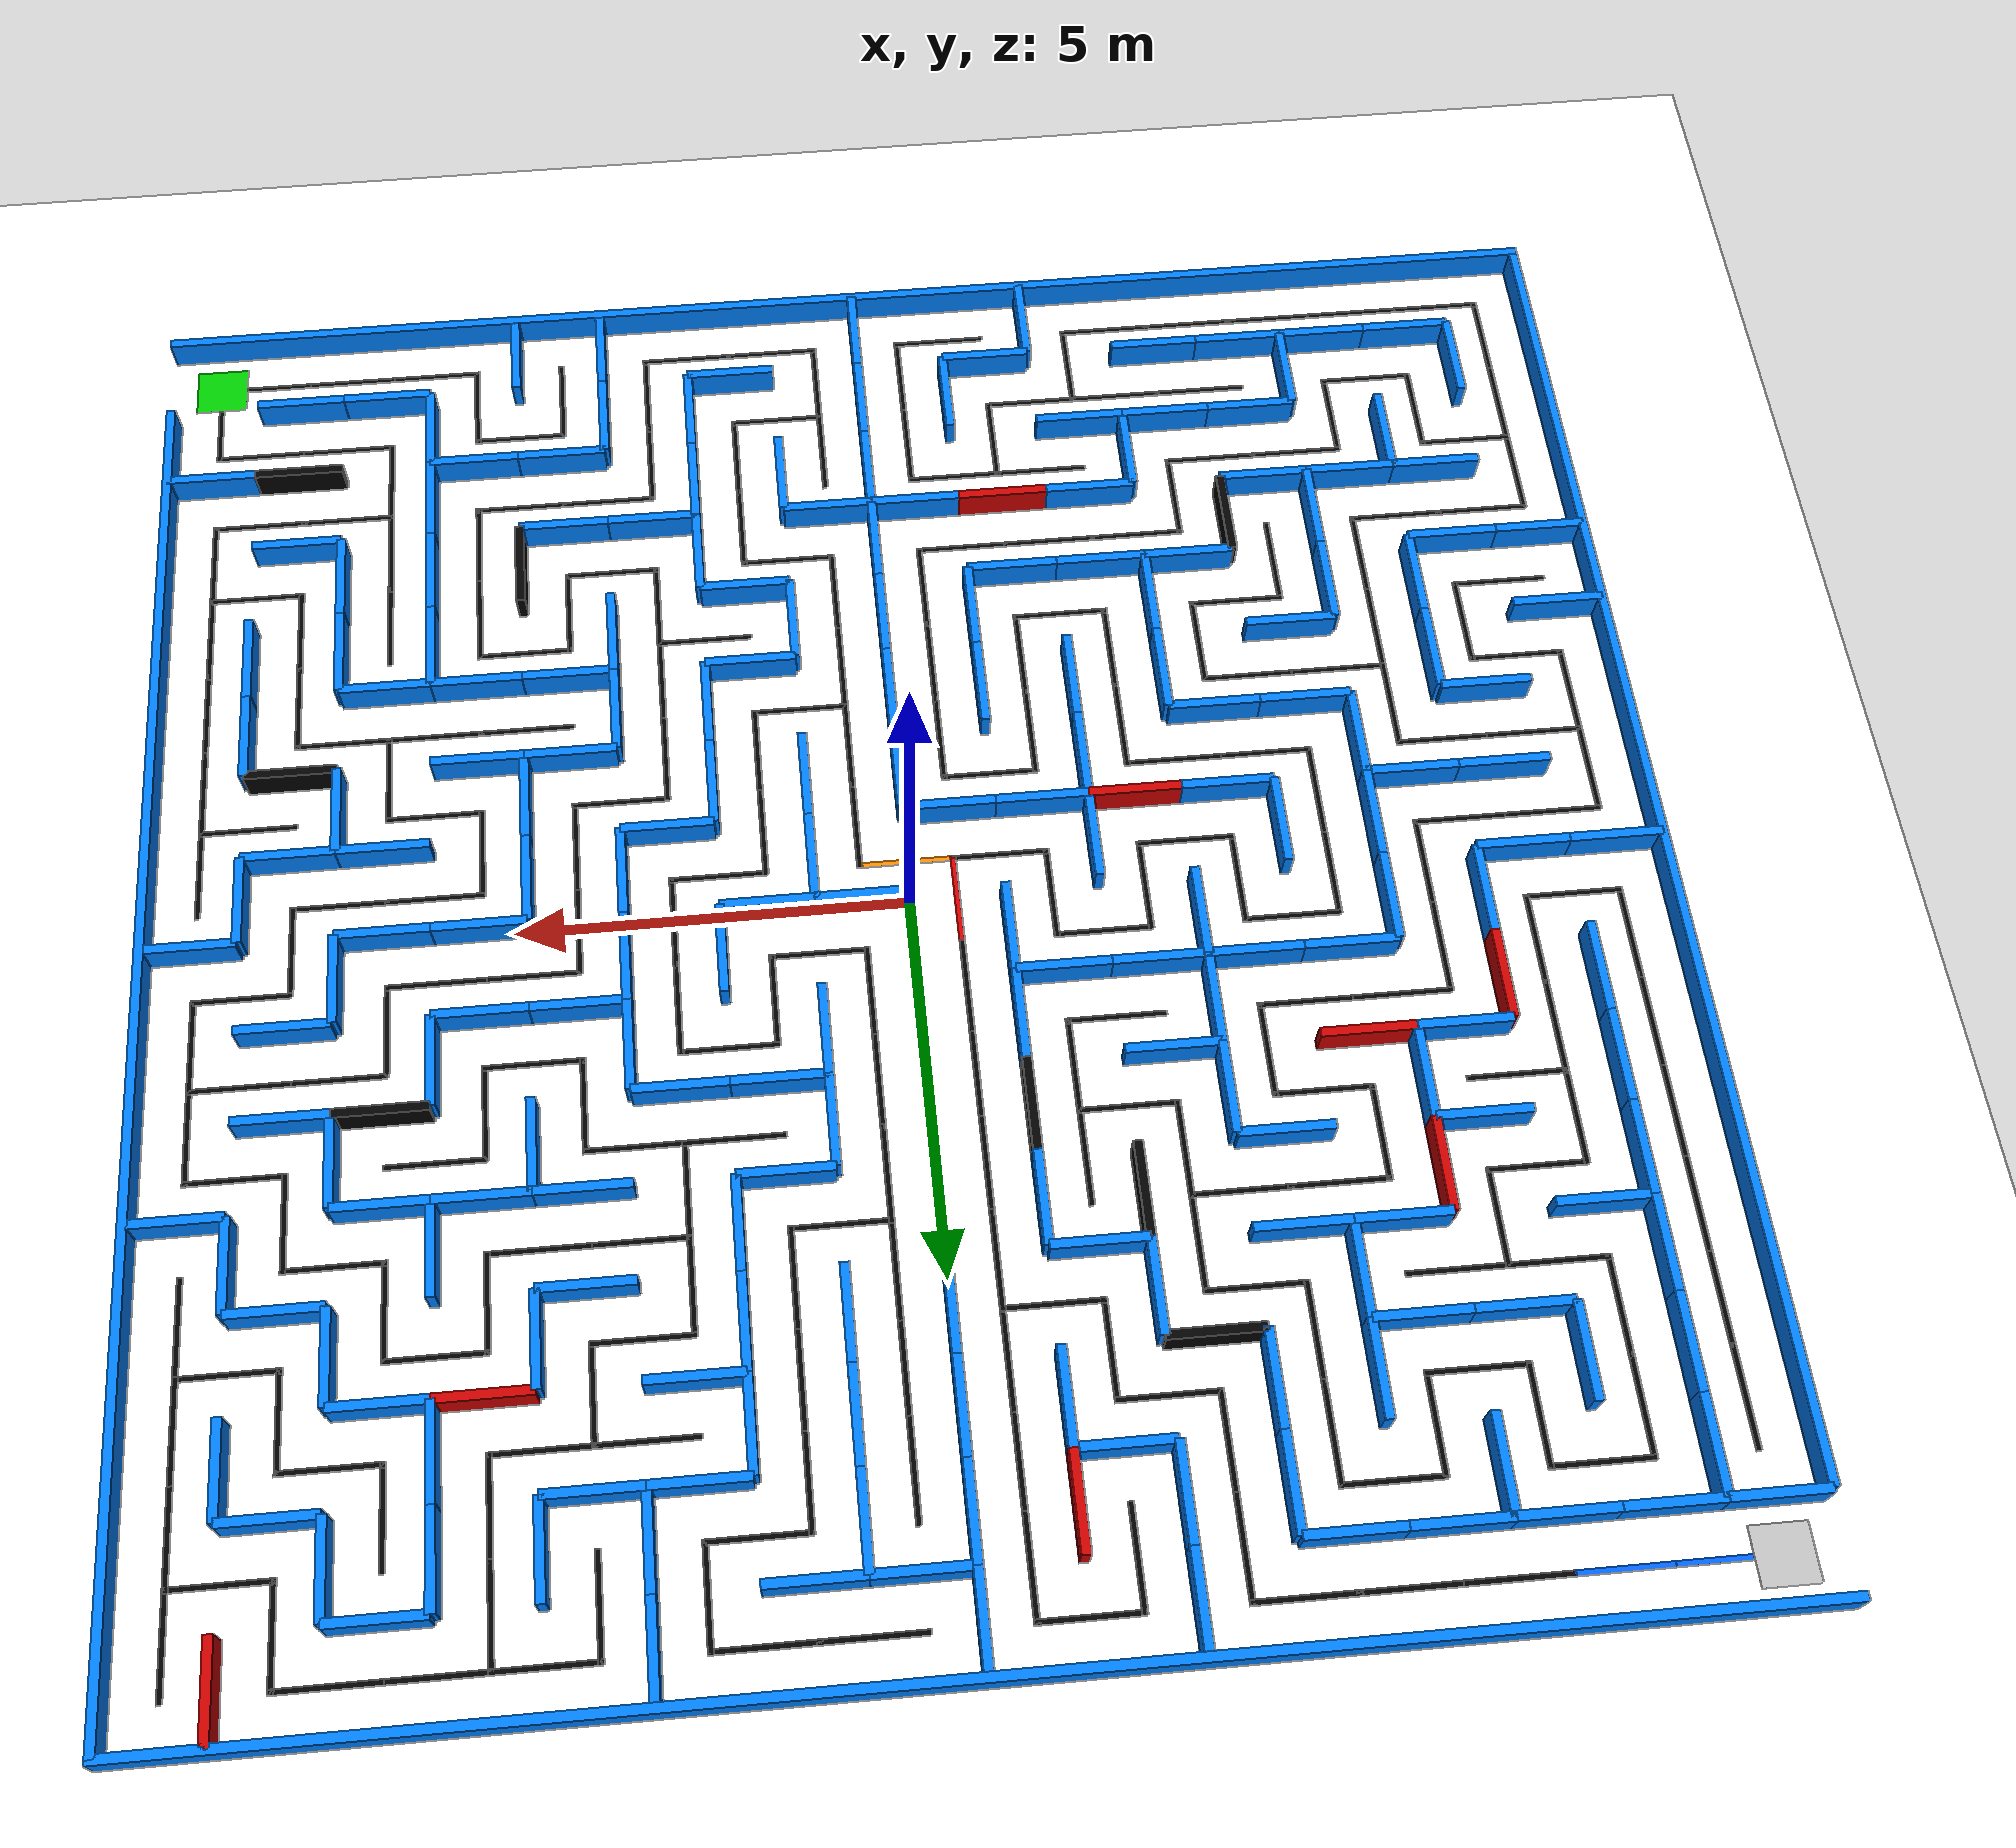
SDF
<?xml version="1.0" ?>
<sdf version="1.6">
  <world name="Map3_FullyLined_16x16">

    <light type="directional" name="sun">
      <cast_shadows>true</cast_shadows>
      <pose>0 0 10 0 0 0</pose>
      <diffuse>1.0 1.0 1.0 1</diffuse>
      <specular>0.5 0.5 0.5 1</specular>
      <direction>-0.5 0.2 -0.9</direction>
    </light>

    <model name="ground_plane">
      <static>true</static>
      <link name="link">
        <collision name="collision"><geometry><plane><normal>0 0 1</normal><size>25.2 25.2</size></plane></geometry></collision>
        <visual name="visual">
          <geometry><plane><normal>0 0 1</normal><size>25.2 25.2</size></plane></geometry>
          <material><ambient>1 1 1 1</ambient><diffuse>1 1 1 1</diffuse></material>
        </visual>
      </link>
    </model>

    <!-- ================= กำแพง (Ultra Sonic สีฟ้า + จุดทดสอบสีดำ/แดง) ================= -->
    <model name="map3_walls">
      <static>true</static>
      <link name="walls_link">

        <collision name="c_out_top"><pose>0.000 9.600 0.2 0 0 0</pose><geometry><box><size>19.320 0.120 0.400</size></box></geometry></collision>
        <visual name="v_out_top"><pose>0.000 9.600 0.2 0 0 0</pose><geometry><box><size>19.320 0.120 0.400</size></box></geometry><material><ambient>0 0.5 1 1</ambient><diffuse>0 0.5 1 1</diffuse></material></visual>
        <collision name="c_out_bot"><pose>0.000 -9.600 0.2 0 0 0</pose><geometry><box><size>19.320 0.120 0.400</size></box></geometry></collision>
        <visual name="v_out_bot"><pose>0.000 -9.600 0.2 0 0 0</pose><geometry><box><size>19.320 0.120 0.400</size></box></geometry><material><ambient>0 0.5 1 1</ambient><diffuse>0 0.5 1 1</diffuse></material></visual>
        <collision name="c_out_left"><pose>-9.600 -0.600 0.2 0 0 0</pose><geometry><box><size>0.120 18.000 0.400</size></box></geometry></collision>
        <visual name="v_out_left"><pose>-9.600 -0.600 0.2 0 0 0</pose><geometry><box><size>0.120 18.000 0.400</size></box></geometry><material><ambient>0 0.5 1 1</ambient><diffuse>0 0.5 1 1</diffuse></material></visual>
        <collision name="c_out_right"><pose>9.600 0.600 0.2 0 0 0</pose><geometry><box><size>0.120 18.000 0.400</size></box></geometry></collision>
        <visual name="v_out_right"><pose>9.600 0.600 0.2 0 0 0</pose><geometry><box><size>0.120 18.000 0.400</size></box></geometry><material><ambient>0 0.5 1 1</ambient><diffuse>0 0.5 1 1</diffuse></material></visual>
        <collision name="c_v_1_1"><pose>-8.400 7.800 0.2 0 0 0</pose><geometry><box><size>0.120 1.200 0.400</size></box></geometry></collision>
        <visual name="v_v_1_1"><pose>-8.400 7.800 0.2 0 0 0</pose><geometry><box><size>0.120 1.200 0.400</size></box></geometry><material><ambient>0 0.5 1 1</ambient><diffuse>0 0.5 1 1</diffuse></material></visual>
        <collision name="c_v_2_1"><pose>-8.400 6.600 0.2 0 0 0</pose><geometry><box><size>0.120 1.200 0.400</size></box></geometry></collision>
        <visual name="v_v_2_1"><pose>-8.400 6.600 0.2 0 0 0</pose><geometry><box><size>0.120 1.200 0.400</size></box></geometry><material><ambient>0 0.5 1 1</ambient><diffuse>0 0.5 1 1</diffuse></material></visual>
        <collision name="c_v_3_1"><pose>-8.400 5.400 0.2 0 0 0</pose><geometry><box><size>0.120 1.200 0.400</size></box></geometry></collision>
        <visual name="v_v_3_1"><pose>-8.400 5.400 0.2 0 0 0</pose><geometry><box><size>0.120 1.200 0.400</size></box></geometry><material><ambient>0 0.5 1 1</ambient><diffuse>0 0.5 1 1</diffuse></material></visual>
        <collision name="c_v_4_1"><pose>-8.400 4.200 0.2 0 0 0</pose><geometry><box><size>0.120 1.200 0.400</size></box></geometry></collision>
        <visual name="v_v_4_1"><pose>-8.400 4.200 0.2 0 0 0</pose><geometry><box><size>0.120 1.200 0.400</size></box></geometry><material><ambient>0 0.5 1 1</ambient><diffuse>0 0.5 1 1</diffuse></material></visual>
        <collision name="c_v_5_1"><pose>-8.400 3.000 0.2 0 0 0</pose><geometry><box><size>0.120 1.200 0.400</size></box></geometry></collision>
        <visual name="v_v_5_1"><pose>-8.400 3.000 0.2 0 0 0</pose><geometry><box><size>0.120 1.200 0.400</size></box></geometry><material><ambient>0 0.5 1 1</ambient><diffuse>0 0.5 1 1</diffuse></material></visual>
        <collision name="c_v_6_1"><pose>-8.400 1.800 0.2 0 0 0</pose><geometry><box><size>0.120 1.200 0.400</size></box></geometry></collision>
        <visual name="v_v_6_1"><pose>-8.400 1.800 0.2 0 0 0</pose><geometry><box><size>0.120 1.200 0.400</size></box></geometry><material><ambient>0 0.5 1 1</ambient><diffuse>0 0.5 1 1</diffuse></material></visual>
        <collision name="c_v_14_1"><pose>-8.400 -7.800 0.2 0 0 0</pose><geometry><box><size>0.120 1.200 0.400</size></box></geometry></collision>
        <visual name="v_v_14_1"><pose>-8.400 -7.800 0.2 0 0 0</pose><geometry><box><size>0.120 1.200 0.400</size></box></geometry><material><ambient>0 0.5 1 1</ambient><diffuse>0 0.5 1 1</diffuse></material></visual>
        <collision name="c_v_2_2"><pose>-7.200 6.600 0.2 0 0 0</pose><geometry><box><size>0.120 1.200 0.400</size></box></geometry></collision>
        <visual name="v_v_2_2"><pose>-7.200 6.600 0.2 0 0 0</pose><geometry><box><size>0.120 1.200 0.400</size></box></geometry><material><ambient>0 0.5 1 1</ambient><diffuse>0 0.5 1 1</diffuse></material></visual>
        <collision name="c_v_6_2"><pose>-7.200 1.800 0.2 0 0 0</pose><geometry><box><size>0.120 1.200 0.400</size></box></geometry></collision>
        <visual name="v_v_6_2"><pose>-7.200 1.800 0.2 0 0 0</pose><geometry><box><size>0.120 1.200 0.400</size></box></geometry><material><ambient>0.8 0 0 1</ambient><diffuse>0.8 0 0 1</diffuse></material></visual>
        <collision name="c_v_7_2"><pose>-7.200 0.600 0.2 0 0 0</pose><geometry><box><size>0.120 1.200 0.400</size></box></geometry></collision>
        <visual name="v_v_7_2"><pose>-7.200 0.600 0.2 0 0 0</pose><geometry><box><size>0.120 1.200 0.400</size></box></geometry><material><ambient>0 0.5 1 1</ambient><diffuse>0 0.5 1 1</diffuse></material></visual>
        <collision name="c_v_10_2"><pose>-7.200 -3.000 0.2 0 0 0</pose><geometry><box><size>0.120 1.200 0.400</size></box></geometry></collision>
        <visual name="v_v_10_2"><pose>-7.200 -3.000 0.2 0 0 0</pose><geometry><box><size>0.120 1.200 0.400</size></box></geometry><material><ambient>0 0.5 1 1</ambient><diffuse>0 0.5 1 1</diffuse></material></visual>
        <collision name="c_v_11_2"><pose>-7.200 -4.200 0.2 0 0 0</pose><geometry><box><size>0.120 1.200 0.400</size></box></geometry></collision>
        <visual name="v_v_11_2"><pose>-7.200 -4.200 0.2 0 0 0</pose><geometry><box><size>0.120 1.200 0.400</size></box></geometry><material><ambient>0 0.5 1 1</ambient><diffuse>0 0.5 1 1</diffuse></material></visual>
        <collision name="c_v_13_2"><pose>-7.200 -6.600 0.2 0 0 0</pose><geometry><box><size>0.120 1.200 0.400</size></box></geometry></collision>
        <visual name="v_v_13_2"><pose>-7.200 -6.600 0.2 0 0 0</pose><geometry><box><size>0.120 1.200 0.400</size></box></geometry><material><ambient>0 0.5 1 1</ambient><diffuse>0 0.5 1 1</diffuse></material></visual>
        <collision name="c_v_1_3"><pose>-6.000 7.800 0.2 0 0 0</pose><geometry><box><size>0.120 1.200 0.400</size></box></geometry></collision>
        <visual name="v_v_1_3"><pose>-6.000 7.800 0.2 0 0 0</pose><geometry><box><size>0.120 1.200 0.400</size></box></geometry><material><ambient>0 0.5 1 1</ambient><diffuse>0 0.5 1 1</diffuse></material></visual>
        <collision name="c_v_4_3"><pose>-6.000 4.200 0.2 0 0 0</pose><geometry><box><size>0.120 1.200 0.400</size></box></geometry></collision>
        <visual name="v_v_4_3"><pose>-6.000 4.200 0.2 0 0 0</pose><geometry><box><size>0.120 1.200 0.400</size></box></geometry><material><ambient>0.8 0 0 1</ambient><diffuse>0.8 0 0 1</diffuse></material></visual>
        <collision name="c_v_5_3"><pose>-6.000 3.000 0.2 0 0 0</pose><geometry><box><size>0.120 1.200 0.400</size></box></geometry></collision>
        <visual name="v_v_5_3"><pose>-6.000 3.000 0.2 0 0 0</pose><geometry><box><size>0.120 1.200 0.400</size></box></geometry><material><ambient>0 0.5 1 1</ambient><diffuse>0 0.5 1 1</diffuse></material></visual>
        <collision name="c_v_7_3"><pose>-6.000 0.600 0.2 0 0 0</pose><geometry><box><size>0.120 1.200 0.400</size></box></geometry></collision>
        <visual name="v_v_7_3"><pose>-6.000 0.600 0.2 0 0 0</pose><geometry><box><size>0.120 1.200 0.400</size></box></geometry><material><ambient>0 0.5 1 1</ambient><diffuse>0 0.5 1 1</diffuse></material></visual>
        <collision name="c_v_8_3"><pose>-6.000 -0.600 0.2 0 0 0</pose><geometry><box><size>0.120 1.200 0.400</size></box></geometry></collision>
        <visual name="v_v_8_3"><pose>-6.000 -0.600 0.2 0 0 0</pose><geometry><box><size>0.120 1.200 0.400</size></box></geometry><material><ambient>0 0.5 1 1</ambient><diffuse>0 0.5 1 1</diffuse></material></visual>
        <collision name="c_v_9_3"><pose>-6.000 -1.800 0.2 0 0 0</pose><geometry><box><size>0.120 1.200 0.400</size></box></geometry></collision>
        <visual name="v_v_9_3"><pose>-6.000 -1.800 0.2 0 0 0</pose><geometry><box><size>0.120 1.200 0.400</size></box></geometry><material><ambient>0 0.5 1 1</ambient><diffuse>0 0.5 1 1</diffuse></material></visual>
        <collision name="c_v_11_3"><pose>-6.000 -4.200 0.2 0 0 0</pose><geometry><box><size>0.120 1.200 0.400</size></box></geometry></collision>
        <visual name="v_v_11_3"><pose>-6.000 -4.200 0.2 0 0 0</pose><geometry><box><size>0.120 1.200 0.400</size></box></geometry><material><ambient>0 0.5 1 1</ambient><diffuse>0 0.5 1 1</diffuse></material></visual>
        <collision name="c_v_12_3"><pose>-6.000 -5.400 0.2 0 0 0</pose><geometry><box><size>0.120 1.200 0.400</size></box></geometry></collision>
        <visual name="v_v_12_3"><pose>-6.000 -5.400 0.2 0 0 0</pose><geometry><box><size>0.120 1.200 0.400</size></box></geometry><material><ambient>0 0.5 1 1</ambient><diffuse>0 0.5 1 1</diffuse></material></visual>
        <collision name="c_v_14_3"><pose>-6.000 -7.800 0.2 0 0 0</pose><geometry><box><size>0.120 1.200 0.400</size></box></geometry></collision>
        <visual name="v_v_14_3"><pose>-6.000 -7.800 0.2 0 0 0</pose><geometry><box><size>0.120 1.200 0.400</size></box></geometry><material><ambient>0 0.5 1 1</ambient><diffuse>0 0.5 1 1</diffuse></material></visual>
        <collision name="c_v_2_4"><pose>-4.800 6.600 0.2 0 0 0</pose><geometry><box><size>0.120 1.200 0.400</size></box></geometry></collision>
        <visual name="v_v_2_4"><pose>-4.800 6.600 0.2 0 0 0</pose><geometry><box><size>0.120 1.200 0.400</size></box></geometry><material><ambient>0 0.5 1 1</ambient><diffuse>0 0.5 1 1</diffuse></material></visual>
        <collision name="c_v_3_4"><pose>-4.800 5.400 0.2 0 0 0</pose><geometry><box><size>0.120 1.200 0.400</size></box></geometry></collision>
        <visual name="v_v_3_4"><pose>-4.800 5.400 0.2 0 0 0</pose><geometry><box><size>0.120 1.200 0.400</size></box></geometry><material><ambient>0 0.5 1 1</ambient><diffuse>0 0.5 1 1</diffuse></material></visual>
        <collision name="c_v_8_4"><pose>-4.800 -0.600 0.2 0 0 0</pose><geometry><box><size>0.120 1.200 0.400</size></box></geometry></collision>
        <visual name="v_v_8_4"><pose>-4.800 -0.600 0.2 0 0 0</pose><geometry><box><size>0.120 1.200 0.400</size></box></geometry><material><ambient>0 0.5 1 1</ambient><diffuse>0 0.5 1 1</diffuse></material></visual>
        <collision name="c_v_12_4"><pose>-4.800 -5.400 0.2 0 0 0</pose><geometry><box><size>0.120 1.200 0.400</size></box></geometry></collision>
        <visual name="v_v_12_4"><pose>-4.800 -5.400 0.2 0 0 0</pose><geometry><box><size>0.120 1.200 0.400</size></box></geometry><material><ambient>0 0 0 1</ambient><diffuse>0 0 0 1</diffuse></material></visual>
        <collision name="c_v_1_5"><pose>-3.600 7.800 0.2 0 0 0</pose><geometry><box><size>0.120 1.200 0.400</size></box></geometry></collision>
        <visual name="v_v_1_5"><pose>-3.600 7.800 0.2 0 0 0</pose><geometry><box><size>0.120 1.200 0.400</size></box></geometry><material><ambient>0 0.5 1 1</ambient><diffuse>0 0.5 1 1</diffuse></material></visual>
        <collision name="c_v_2_5"><pose>-3.600 6.600 0.2 0 0 0</pose><geometry><box><size>0.120 1.200 0.400</size></box></geometry></collision>
        <visual name="v_v_2_5"><pose>-3.600 6.600 0.2 0 0 0</pose><geometry><box><size>0.120 1.200 0.400</size></box></geometry><material><ambient>0 0.5 1 1</ambient><diffuse>0 0.5 1 1</diffuse></material></visual>
        <collision name="c_v_5_5"><pose>-3.600 3.000 0.2 0 0 0</pose><geometry><box><size>0.120 1.200 0.400</size></box></geometry></collision>
        <visual name="v_v_5_5"><pose>-3.600 3.000 0.2 0 0 0</pose><geometry><box><size>0.120 1.200 0.400</size></box></geometry><material><ambient>0 0.5 1 1</ambient><diffuse>0 0.5 1 1</diffuse></material></visual>
        <collision name="c_v_6_5"><pose>-3.600 1.800 0.2 0 0 0</pose><geometry><box><size>0.120 1.200 0.400</size></box></geometry></collision>
        <visual name="v_v_6_5"><pose>-3.600 1.800 0.2 0 0 0</pose><geometry><box><size>0.120 1.200 0.400</size></box></geometry><material><ambient>0 0.5 1 1</ambient><diffuse>0 0.5 1 1</diffuse></material></visual>
        <collision name="c_v_7_5"><pose>-3.600 0.600 0.2 0 0 0</pose><geometry><box><size>0.120 1.200 0.400</size></box></geometry></collision>
        <visual name="v_v_7_5"><pose>-3.600 0.600 0.2 0 0 0</pose><geometry><box><size>0.120 1.200 0.400</size></box></geometry><material><ambient>0 0.5 1 1</ambient><diffuse>0 0.5 1 1</diffuse></material></visual>
        <collision name="c_v_10_5"><pose>-3.600 -3.000 0.2 0 0 0</pose><geometry><box><size>0.120 1.200 0.400</size></box></geometry></collision>
        <visual name="v_v_10_5"><pose>-3.600 -3.000 0.2 0 0 0</pose><geometry><box><size>0.120 1.200 0.400</size></box></geometry><material><ambient>0 0.5 1 1</ambient><diffuse>0 0.5 1 1</diffuse></material></visual>
        <collision name="c_v_11_5"><pose>-3.600 -4.200 0.2 0 0 0</pose><geometry><box><size>0.120 1.200 0.400</size></box></geometry></collision>
        <visual name="v_v_11_5"><pose>-3.600 -4.200 0.2 0 0 0</pose><geometry><box><size>0.120 1.200 0.400</size></box></geometry><material><ambient>0 0.5 1 1</ambient><diffuse>0 0.5 1 1</diffuse></material></visual>
        <collision name="c_v_13_5"><pose>-3.600 -6.600 0.2 0 0 0</pose><geometry><box><size>0.120 1.200 0.400</size></box></geometry></collision>
        <visual name="v_v_13_5"><pose>-3.600 -6.600 0.2 0 0 0</pose><geometry><box><size>0.120 1.200 0.400</size></box></geometry><material><ambient>0 0.5 1 1</ambient><diffuse>0 0.5 1 1</diffuse></material></visual>
        <collision name="c_v_0_6"><pose>-2.400 9.000 0.2 0 0 0</pose><geometry><box><size>0.120 1.200 0.400</size></box></geometry></collision>
        <visual name="v_v_0_6"><pose>-2.400 9.000 0.2 0 0 0</pose><geometry><box><size>0.120 1.200 0.400</size></box></geometry><material><ambient>0 0.5 1 1</ambient><diffuse>0 0.5 1 1</diffuse></material></visual>
        <collision name="c_v_1_6"><pose>-2.400 7.800 0.2 0 0 0</pose><geometry><box><size>0.120 1.200 0.400</size></box></geometry></collision>
        <visual name="v_v_1_6"><pose>-2.400 7.800 0.2 0 0 0</pose><geometry><box><size>0.120 1.200 0.400</size></box></geometry><material><ambient>0 0.5 1 1</ambient><diffuse>0 0.5 1 1</diffuse></material></visual>
        <collision name="c_v_3_6"><pose>-2.400 5.400 0.2 0 0 0</pose><geometry><box><size>0.120 1.200 0.400</size></box></geometry></collision>
        <visual name="v_v_3_6"><pose>-2.400 5.400 0.2 0 0 0</pose><geometry><box><size>0.120 1.200 0.400</size></box></geometry><material><ambient>0 0.5 1 1</ambient><diffuse>0 0.5 1 1</diffuse></material></visual>
        <collision name="c_v_4_6"><pose>-2.400 4.200 0.2 0 0 0</pose><geometry><box><size>0.120 1.200 0.400</size></box></geometry></collision>
        <visual name="v_v_4_6"><pose>-2.400 4.200 0.2 0 0 0</pose><geometry><box><size>0.120 1.200 0.400</size></box></geometry><material><ambient>0 0 0 1</ambient><diffuse>0 0 0 1</diffuse></material></visual>
        <collision name="c_v_8_6"><pose>-2.400 -0.600 0.2 0 0 0</pose><geometry><box><size>0.120 1.200 0.400</size></box></geometry></collision>
        <visual name="v_v_8_6"><pose>-2.400 -0.600 0.2 0 0 0</pose><geometry><box><size>0.120 1.200 0.400</size></box></geometry><material><ambient>0 0.5 1 1</ambient><diffuse>0 0.5 1 1</diffuse></material></visual>
        <collision name="c_v_9_6"><pose>-2.400 -1.800 0.2 0 0 0</pose><geometry><box><size>0.120 1.200 0.400</size></box></geometry></collision>
        <visual name="v_v_9_6"><pose>-2.400 -1.800 0.2 0 0 0</pose><geometry><box><size>0.120 1.200 0.400</size></box></geometry><material><ambient>0 0.5 1 1</ambient><diffuse>0 0.5 1 1</diffuse></material></visual>
        <collision name="c_v_10_6"><pose>-2.400 -3.000 0.2 0 0 0</pose><geometry><box><size>0.120 1.200 0.400</size></box></geometry></collision>
        <visual name="v_v_10_6"><pose>-2.400 -3.000 0.2 0 0 0</pose><geometry><box><size>0.120 1.200 0.400</size></box></geometry><material><ambient>0 0.5 1 1</ambient><diffuse>0 0.5 1 1</diffuse></material></visual>
        <collision name="c_v_15_6"><pose>-2.400 -9.000 0.2 0 0 0</pose><geometry><box><size>0.120 1.200 0.400</size></box></geometry></collision>
        <visual name="v_v_15_6"><pose>-2.400 -9.000 0.2 0 0 0</pose><geometry><box><size>0.120 1.200 0.400</size></box></geometry><material><ambient>0 0.5 1 1</ambient><diffuse>0 0.5 1 1</diffuse></material></visual>
        <collision name="c_v_1_7"><pose>-1.200 7.800 0.2 0 0 0</pose><geometry><box><size>0.120 1.200 0.400</size></box></geometry></collision>
        <visual name="v_v_1_7"><pose>-1.200 7.800 0.2 0 0 0</pose><geometry><box><size>0.120 1.200 0.400</size></box></geometry><material><ambient>0.8 0 0 1</ambient><diffuse>0.8 0 0 1</diffuse></material></visual>
        <collision name="c_v_2_7"><pose>-1.200 6.600 0.2 0 0 0</pose><geometry><box><size>0.120 1.200 0.400</size></box></geometry></collision>
        <visual name="v_v_2_7"><pose>-1.200 6.600 0.2 0 0 0</pose><geometry><box><size>0.120 1.200 0.400</size></box></geometry><material><ambient>0 0.5 1 1</ambient><diffuse>0 0.5 1 1</diffuse></material></visual>
        <collision name="c_v_4_7"><pose>-1.200 4.200 0.2 0 0 0</pose><geometry><box><size>0.120 1.200 0.400</size></box></geometry></collision>
        <visual name="v_v_4_7"><pose>-1.200 4.200 0.2 0 0 0</pose><geometry><box><size>0.120 1.200 0.400</size></box></geometry><material><ambient>0 0.5 1 1</ambient><diffuse>0 0.5 1 1</diffuse></material></visual>
        <collision name="c_v_5_7"><pose>-1.200 3.000 0.2 0 0 0</pose><geometry><box><size>0.120 1.200 0.400</size></box></geometry></collision>
        <visual name="v_v_5_7"><pose>-1.200 3.000 0.2 0 0 0</pose><geometry><box><size>0.120 1.200 0.400</size></box></geometry><material><ambient>0 0 0 1</ambient><diffuse>0 0 0 1</diffuse></material></visual>
        <collision name="c_v_6_7"><pose>-1.200 1.800 0.2 0 0 0</pose><geometry><box><size>0.120 1.200 0.400</size></box></geometry></collision>
        <visual name="v_v_6_7"><pose>-1.200 1.800 0.2 0 0 0</pose><geometry><box><size>0.120 1.200 0.400</size></box></geometry><material><ambient>0 0.5 1 1</ambient><diffuse>0 0.5 1 1</diffuse></material></visual>
        <collision name="c_v_7_7"><pose>-1.200 0.600 0.2 0 0 0</pose><geometry><box><size>0.120 1.200 0.400</size></box></geometry></collision>
        <visual name="v_v_7_7"><pose>-1.200 0.600 0.2 0 0 0</pose><geometry><box><size>0.120 1.200 0.400</size></box></geometry><material><ambient>0 0.5 1 1</ambient><diffuse>0 0.5 1 1</diffuse></material></visual>
        <collision name="c_v_10_7"><pose>-1.200 -3.000 0.2 0 0 0</pose><geometry><box><size>0.120 1.200 0.400</size></box></geometry></collision>
        <visual name="v_v_10_7"><pose>-1.200 -3.000 0.2 0 0 0</pose><geometry><box><size>0.120 1.200 0.400</size></box></geometry><material><ambient>0 0.5 1 1</ambient><diffuse>0 0.5 1 1</diffuse></material></visual>
        <collision name="c_v_11_7"><pose>-1.200 -4.200 0.2 0 0 0</pose><geometry><box><size>0.120 1.200 0.400</size></box></geometry></collision>
        <visual name="v_v_11_7"><pose>-1.200 -4.200 0.2 0 0 0</pose><geometry><box><size>0.120 1.200 0.400</size></box></geometry><material><ambient>0 0.5 1 1</ambient><diffuse>0 0.5 1 1</diffuse></material></visual>
        <collision name="c_v_14_7"><pose>-1.200 -7.800 0.2 0 0 0</pose><geometry><box><size>0.120 1.200 0.400</size></box></geometry></collision>
        <visual name="v_v_14_7"><pose>-1.200 -7.800 0.2 0 0 0</pose><geometry><box><size>0.120 1.200 0.400</size></box></geometry><material><ambient>0 0.5 1 1</ambient><diffuse>0 0.5 1 1</diffuse></material></visual>
        <collision name="c_v_0_8"><pose>0.000 9.000 0.2 0 0 0</pose><geometry><box><size>0.120 1.200 0.400</size></box></geometry></collision>
        <visual name="v_v_0_8"><pose>0.000 9.000 0.2 0 0 0</pose><geometry><box><size>0.120 1.200 0.400</size></box></geometry><material><ambient>0 0.5 1 1</ambient><diffuse>0 0.5 1 1</diffuse></material></visual>
        <collision name="c_v_1_8"><pose>0.000 7.800 0.2 0 0 0</pose><geometry><box><size>0.120 1.200 0.400</size></box></geometry></collision>
        <visual name="v_v_1_8"><pose>0.000 7.800 0.2 0 0 0</pose><geometry><box><size>0.120 1.200 0.400</size></box></geometry><material><ambient>0 0.5 1 1</ambient><diffuse>0 0.5 1 1</diffuse></material></visual>
        <collision name="c_v_2_8"><pose>0.000 6.600 0.2 0 0 0</pose><geometry><box><size>0.120 1.200 0.400</size></box></geometry></collision>
        <visual name="v_v_2_8"><pose>0.000 6.600 0.2 0 0 0</pose><geometry><box><size>0.120 1.200 0.400</size></box></geometry><material><ambient>0 0.5 1 1</ambient><diffuse>0 0.5 1 1</diffuse></material></visual>
        <collision name="c_v_3_8"><pose>0.000 5.400 0.2 0 0 0</pose><geometry><box><size>0.120 1.200 0.400</size></box></geometry></collision>
        <visual name="v_v_3_8"><pose>0.000 5.400 0.2 0 0 0</pose><geometry><box><size>0.120 1.200 0.400</size></box></geometry><material><ambient>0 0.5 1 1</ambient><diffuse>0 0.5 1 1</diffuse></material></visual>
        <collision name="c_v_4_8"><pose>0.000 4.200 0.2 0 0 0</pose><geometry><box><size>0.120 1.200 0.400</size></box></geometry></collision>
        <visual name="v_v_4_8"><pose>0.000 4.200 0.2 0 0 0</pose><geometry><box><size>0.120 1.200 0.400</size></box></geometry><material><ambient>0 0.5 1 1</ambient><diffuse>0 0.5 1 1</diffuse></material></visual>
        <collision name="c_v_5_8"><pose>0.000 3.000 0.2 0 0 0</pose><geometry><box><size>0.120 1.200 0.400</size></box></geometry></collision>
        <visual name="v_v_5_8"><pose>0.000 3.000 0.2 0 0 0</pose><geometry><box><size>0.120 1.200 0.400</size></box></geometry><material><ambient>0 0.5 1 1</ambient><diffuse>0 0.5 1 1</diffuse></material></visual>
        <collision name="c_v_6_8"><pose>0.000 1.800 0.2 0 0 0</pose><geometry><box><size>0.120 1.200 0.400</size></box></geometry></collision>
        <visual name="v_v_6_8"><pose>0.000 1.800 0.2 0 0 0</pose><geometry><box><size>0.120 1.200 0.400</size></box></geometry><material><ambient>0 0.5 1 1</ambient><diffuse>0 0.5 1 1</diffuse></material></visual>
        <collision name="c_v_7_8"><pose>0.000 0.600 0.2 0 0 0</pose><geometry><box><size>0.120 1.200 0.400</size></box></geometry></collision>
        <visual name="v_v_7_8"><pose>0.000 0.600 0.2 0 0 0</pose><geometry><box><size>0.120 1.200 0.400</size></box></geometry><material><ambient>0 0.5 1 1</ambient><diffuse>0 0.5 1 1</diffuse></material></visual>
        <collision name="c_v_9_8"><pose>0.000 -1.800 0.2 0 0 0</pose><geometry><box><size>0.120 1.200 0.400</size></box></geometry></collision>
        <visual name="v_v_9_8"><pose>0.000 -1.800 0.2 0 0 0</pose><geometry><box><size>0.120 1.200 0.400</size></box></geometry><material><ambient>0 0.5 1 1</ambient><diffuse>0 0.5 1 1</diffuse></material></visual>
        <collision name="c_v_10_8"><pose>0.000 -3.000 0.2 0 0 0</pose><geometry><box><size>0.120 1.200 0.400</size></box></geometry></collision>
        <visual name="v_v_10_8"><pose>0.000 -3.000 0.2 0 0 0</pose><geometry><box><size>0.120 1.200 0.400</size></box></geometry><material><ambient>0 0.5 1 1</ambient><diffuse>0 0.5 1 1</diffuse></material></visual>
        <collision name="c_v_11_8"><pose>0.000 -4.200 0.2 0 0 0</pose><geometry><box><size>0.120 1.200 0.400</size></box></geometry></collision>
        <visual name="v_v_11_8"><pose>0.000 -4.200 0.2 0 0 0</pose><geometry><box><size>0.120 1.200 0.400</size></box></geometry><material><ambient>0 0.5 1 1</ambient><diffuse>0 0.5 1 1</diffuse></material></visual>
        <collision name="c_v_12_8"><pose>0.000 -5.400 0.2 0 0 0</pose><geometry><box><size>0.120 1.200 0.400</size></box></geometry></collision>
        <visual name="v_v_12_8"><pose>0.000 -5.400 0.2 0 0 0</pose><geometry><box><size>0.120 1.200 0.400</size></box></geometry><material><ambient>0 0.5 1 1</ambient><diffuse>0 0.5 1 1</diffuse></material></visual>
        <collision name="c_v_13_8"><pose>0.000 -6.600 0.2 0 0 0</pose><geometry><box><size>0.120 1.200 0.400</size></box></geometry></collision>
        <visual name="v_v_13_8"><pose>0.000 -6.600 0.2 0 0 0</pose><geometry><box><size>0.120 1.200 0.400</size></box></geometry><material><ambient>0 0.5 1 1</ambient><diffuse>0 0.5 1 1</diffuse></material></visual>
        <collision name="c_v_14_8"><pose>0.000 -7.800 0.2 0 0 0</pose><geometry><box><size>0.120 1.200 0.400</size></box></geometry></collision>
        <visual name="v_v_14_8"><pose>0.000 -7.800 0.2 0 0 0</pose><geometry><box><size>0.120 1.200 0.400</size></box></geometry><material><ambient>0 0.5 1 1</ambient><diffuse>0 0.5 1 1</diffuse></material></visual>
        <collision name="c_v_15_8"><pose>0.000 -9.000 0.2 0 0 0</pose><geometry><box><size>0.120 1.200 0.400</size></box></geometry></collision>
        <visual name="v_v_15_8"><pose>0.000 -9.000 0.2 0 0 0</pose><geometry><box><size>0.120 1.200 0.400</size></box></geometry><material><ambient>0 0.5 1 1</ambient><diffuse>0 0.5 1 1</diffuse></material></visual>
        <collision name="c_v_1_9"><pose>1.200 7.800 0.2 0 0 0</pose><geometry><box><size>0.120 1.200 0.400</size></box></geometry></collision>
        <visual name="v_v_1_9"><pose>1.200 7.800 0.2 0 0 0</pose><geometry><box><size>0.120 1.200 0.400</size></box></geometry><material><ambient>0 0.5 1 1</ambient><diffuse>0 0.5 1 1</diffuse></material></visual>
        <collision name="c_v_2_9"><pose>1.200 6.600 0.2 0 0 0</pose><geometry><box><size>0.120 1.200 0.400</size></box></geometry></collision>
        <visual name="v_v_2_9"><pose>1.200 6.600 0.2 0 0 0</pose><geometry><box><size>0.120 1.200 0.400</size></box></geometry><material><ambient>0 0.5 1 1</ambient><diffuse>0 0.5 1 1</diffuse></material></visual>
        <collision name="c_v_3_9"><pose>1.200 5.400 0.2 0 0 0</pose><geometry><box><size>0.120 1.200 0.400</size></box></geometry></collision>
        <visual name="v_v_3_9"><pose>1.200 5.400 0.2 0 0 0</pose><geometry><box><size>0.120 1.200 0.400</size></box></geometry><material><ambient>0 0.5 1 1</ambient><diffuse>0 0.5 1 1</diffuse></material></visual>
        <collision name="c_v_5_9"><pose>1.200 3.000 0.2 0 0 0</pose><geometry><box><size>0.120 1.200 0.400</size></box></geometry></collision>
        <visual name="v_v_5_9"><pose>1.200 3.000 0.2 0 0 0</pose><geometry><box><size>0.120 1.200 0.400</size></box></geometry><material><ambient>0 0.5 1 1</ambient><diffuse>0 0.5 1 1</diffuse></material></visual>
        <collision name="c_v_6_9"><pose>1.200 1.800 0.2 0 0 0</pose><geometry><box><size>0.120 1.200 0.400</size></box></geometry></collision>
        <visual name="v_v_6_9"><pose>1.200 1.800 0.2 0 0 0</pose><geometry><box><size>0.120 1.200 0.400</size></box></geometry><material><ambient>0 0.5 1 1</ambient><diffuse>0 0.5 1 1</diffuse></material></visual>
        <collision name="c_v_8_9"><pose>1.200 -0.600 0.2 0 0 0</pose><geometry><box><size>0.120 1.200 0.400</size></box></geometry></collision>
        <visual name="v_v_8_9"><pose>1.200 -0.600 0.2 0 0 0</pose><geometry><box><size>0.120 1.200 0.400</size></box></geometry><material><ambient>0 0.5 1 1</ambient><diffuse>0 0.5 1 1</diffuse></material></visual>
        <collision name="c_v_9_9"><pose>1.200 -1.800 0.2 0 0 0</pose><geometry><box><size>0.120 1.200 0.400</size></box></geometry></collision>
        <visual name="v_v_9_9"><pose>1.200 -1.800 0.2 0 0 0</pose><geometry><box><size>0.120 1.200 0.400</size></box></geometry><material><ambient>0 0.5 1 1</ambient><diffuse>0 0.5 1 1</diffuse></material></visual>
        <collision name="c_v_11_9"><pose>1.200 -4.200 0.2 0 0 0</pose><geometry><box><size>0.120 1.200 0.400</size></box></geometry></collision>
        <visual name="v_v_11_9"><pose>1.200 -4.200 0.2 0 0 0</pose><geometry><box><size>0.120 1.200 0.400</size></box></geometry><material><ambient>0 0.5 1 1</ambient><diffuse>0 0.5 1 1</diffuse></material></visual>
        <collision name="c_v_13_9"><pose>1.200 -6.600 0.2 0 0 0</pose><geometry><box><size>0.120 1.200 0.400</size></box></geometry></collision>
        <visual name="v_v_13_9"><pose>1.200 -6.600 0.2 0 0 0</pose><geometry><box><size>0.120 1.200 0.400</size></box></geometry><material><ambient>0 0.5 1 1</ambient><diffuse>0 0.5 1 1</diffuse></material></visual>
        <collision name="c_v_2_10"><pose>2.400 6.600 0.2 0 0 0</pose><geometry><box><size>0.120 1.200 0.400</size></box></geometry></collision>
        <visual name="v_v_2_10"><pose>2.400 6.600 0.2 0 0 0</pose><geometry><box><size>0.120 1.200 0.400</size></box></geometry><material><ambient>0 0.5 1 1</ambient><diffuse>0 0.5 1 1</diffuse></material></visual>
        <collision name="c_v_3_10"><pose>2.400 5.400 0.2 0 0 0</pose><geometry><box><size>0.120 1.200 0.400</size></box></geometry></collision>
        <visual name="v_v_3_10"><pose>2.400 5.400 0.2 0 0 0</pose><geometry><box><size>0.120 1.200 0.400</size></box></geometry><material><ambient>0 0.5 1 1</ambient><diffuse>0 0.5 1 1</diffuse></material></visual>
        <collision name="c_v_4_10"><pose>2.400 4.200 0.2 0 0 0</pose><geometry><box><size>0.120 1.200 0.400</size></box></geometry></collision>
        <visual name="v_v_4_10"><pose>2.400 4.200 0.2 0 0 0</pose><geometry><box><size>0.120 1.200 0.400</size></box></geometry><material><ambient>0 0.5 1 1</ambient><diffuse>0 0.5 1 1</diffuse></material></visual>
        <collision name="c_v_7_10"><pose>2.400 0.600 0.2 0 0 0</pose><geometry><box><size>0.120 1.200 0.400</size></box></geometry></collision>
        <visual name="v_v_7_10"><pose>2.400 0.600 0.2 0 0 0</pose><geometry><box><size>0.120 1.200 0.400</size></box></geometry><material><ambient>0 0.5 1 1</ambient><diffuse>0 0.5 1 1</diffuse></material></visual>
        <collision name="c_v_9_10"><pose>2.400 -1.800 0.2 0 0 0</pose><geometry><box><size>0.120 1.200 0.400</size></box></geometry></collision>
        <visual name="v_v_9_10"><pose>2.400 -1.800 0.2 0 0 0</pose><geometry><box><size>0.120 1.200 0.400</size></box></geometry><material><ambient>0 0.5 1 1</ambient><diffuse>0 0.5 1 1</diffuse></material></visual>
        <collision name="c_v_10_10"><pose>2.400 -3.000 0.2 0 0 0</pose><geometry><box><size>0.120 1.200 0.400</size></box></geometry></collision>
        <visual name="v_v_10_10"><pose>2.400 -3.000 0.2 0 0 0</pose><geometry><box><size>0.120 1.200 0.400</size></box></geometry><material><ambient>0 0.5 1 1</ambient><diffuse>0 0.5 1 1</diffuse></material></visual>
        <collision name="c_v_12_10"><pose>2.400 -5.400 0.2 0 0 0</pose><geometry><box><size>0.120 1.200 0.400</size></box></geometry></collision>
        <visual name="v_v_12_10"><pose>2.400 -5.400 0.2 0 0 0</pose><geometry><box><size>0.120 1.200 0.400</size></box></geometry><material><ambient>0 0.5 1 1</ambient><diffuse>0 0.5 1 1</diffuse></material></visual>
        <collision name="c_v_13_10"><pose>2.400 -6.600 0.2 0 0 0</pose><geometry><box><size>0.120 1.200 0.400</size></box></geometry></collision>
        <visual name="v_v_13_10"><pose>2.400 -6.600 0.2 0 0 0</pose><geometry><box><size>0.120 1.200 0.400</size></box></geometry><material><ambient>0 0.5 1 1</ambient><diffuse>0 0.5 1 1</diffuse></material></visual>
        <collision name="c_v_14_10"><pose>2.400 -7.800 0.2 0 0 0</pose><geometry><box><size>0.120 1.200 0.400</size></box></geometry></collision>
        <visual name="v_v_14_10"><pose>2.400 -7.800 0.2 0 0 0</pose><geometry><box><size>0.120 1.200 0.400</size></box></geometry><material><ambient>0 0.5 1 1</ambient><diffuse>0 0.5 1 1</diffuse></material></visual>
        <collision name="c_v_0_11"><pose>3.600 9.000 0.2 0 0 0</pose><geometry><box><size>0.120 1.200 0.400</size></box></geometry></collision>
        <visual name="v_v_0_11"><pose>3.600 9.000 0.2 0 0 0</pose><geometry><box><size>0.120 1.200 0.400</size></box></geometry><material><ambient>0 0.5 1 1</ambient><diffuse>0 0.5 1 1</diffuse></material></visual>
        <collision name="c_v_1_11"><pose>3.600 7.800 0.2 0 0 0</pose><geometry><box><size>0.120 1.200 0.400</size></box></geometry></collision>
        <visual name="v_v_1_11"><pose>3.600 7.800 0.2 0 0 0</pose><geometry><box><size>0.120 1.200 0.400</size></box></geometry><material><ambient>0 0.5 1 1</ambient><diffuse>0 0.5 1 1</diffuse></material></visual>
        <collision name="c_v_6_11"><pose>3.600 1.800 0.2 0 0 0</pose><geometry><box><size>0.120 1.200 0.400</size></box></geometry></collision>
        <visual name="v_v_6_11"><pose>3.600 1.800 0.2 0 0 0</pose><geometry><box><size>0.120 1.200 0.400</size></box></geometry><material><ambient>0 0.5 1 1</ambient><diffuse>0 0.5 1 1</diffuse></material></visual>
        <collision name="c_v_7_11"><pose>3.600 0.600 0.2 0 0 0</pose><geometry><box><size>0.120 1.200 0.400</size></box></geometry></collision>
        <visual name="v_v_7_11"><pose>3.600 0.600 0.2 0 0 0</pose><geometry><box><size>0.120 1.200 0.400</size></box></geometry><material><ambient>0 0.5 1 1</ambient><diffuse>0 0.5 1 1</diffuse></material></visual>
        <collision name="c_v_8_11"><pose>3.600 -0.600 0.2 0 0 0</pose><geometry><box><size>0.120 1.200 0.400</size></box></geometry></collision>
        <visual name="v_v_8_11"><pose>3.600 -0.600 0.2 0 0 0</pose><geometry><box><size>0.120 1.200 0.400</size></box></geometry><material><ambient>0 0.5 1 1</ambient><diffuse>0 0.5 1 1</diffuse></material></visual>
        <collision name="c_v_10_11"><pose>3.600 -3.000 0.2 0 0 0</pose><geometry><box><size>0.120 1.200 0.400</size></box></geometry></collision>
        <visual name="v_v_10_11"><pose>3.600 -3.000 0.2 0 0 0</pose><geometry><box><size>0.120 1.200 0.400</size></box></geometry><material><ambient>0 0.5 1 1</ambient><diffuse>0 0.5 1 1</diffuse></material></visual>
        <collision name="c_v_11_11"><pose>3.600 -4.200 0.2 0 0 0</pose><geometry><box><size>0.120 1.200 0.400</size></box></geometry></collision>
        <visual name="v_v_11_11"><pose>3.600 -4.200 0.2 0 0 0</pose><geometry><box><size>0.120 1.200 0.400</size></box></geometry><material><ambient>0 0.5 1 1</ambient><diffuse>0 0.5 1 1</diffuse></material></visual>
        <collision name="c_v_14_11"><pose>3.600 -7.800 0.2 0 0 0</pose><geometry><box><size>0.120 1.200 0.400</size></box></geometry></collision>
        <visual name="v_v_14_11"><pose>3.600 -7.800 0.2 0 0 0</pose><geometry><box><size>0.120 1.200 0.400</size></box></geometry><material><ambient>0 0.5 1 1</ambient><diffuse>0 0.5 1 1</diffuse></material></visual>
        <collision name="c_v_15_11"><pose>3.600 -9.000 0.2 0 0 0</pose><geometry><box><size>0.120 1.200 0.400</size></box></geometry></collision>
        <visual name="v_v_15_11"><pose>3.600 -9.000 0.2 0 0 0</pose><geometry><box><size>0.120 1.200 0.400</size></box></geometry><material><ambient>0 0.5 1 1</ambient><diffuse>0 0.5 1 1</diffuse></material></visual>
        <collision name="c_v_1_12"><pose>4.800 7.800 0.2 0 0 0</pose><geometry><box><size>0.120 1.200 0.400</size></box></geometry></collision>
        <visual name="v_v_1_12"><pose>4.800 7.800 0.2 0 0 0</pose><geometry><box><size>0.120 1.200 0.400</size></box></geometry><material><ambient>0 0.5 1 1</ambient><diffuse>0 0.5 1 1</diffuse></material></visual>
        <collision name="c_v_3_12"><pose>4.800 5.400 0.2 0 0 0</pose><geometry><box><size>0.120 1.200 0.400</size></box></geometry></collision>
        <visual name="v_v_3_12"><pose>4.800 5.400 0.2 0 0 0</pose><geometry><box><size>0.120 1.200 0.400</size></box></geometry><material><ambient>0 0.5 1 1</ambient><diffuse>0 0.5 1 1</diffuse></material></visual>
        <collision name="c_v_5_12"><pose>4.800 3.000 0.2 0 0 0</pose><geometry><box><size>0.120 1.200 0.400</size></box></geometry></collision>
        <visual name="v_v_5_12"><pose>4.800 3.000 0.2 0 0 0</pose><geometry><box><size>0.120 1.200 0.400</size></box></geometry><material><ambient>0 0.5 1 1</ambient><diffuse>0 0.5 1 1</diffuse></material></visual>
        <collision name="c_v_8_12"><pose>4.800 -0.600 0.2 0 0 0</pose><geometry><box><size>0.120 1.200 0.400</size></box></geometry></collision>
        <visual name="v_v_8_12"><pose>4.800 -0.600 0.2 0 0 0</pose><geometry><box><size>0.120 1.200 0.400</size></box></geometry><material><ambient>0 0.5 1 1</ambient><diffuse>0 0.5 1 1</diffuse></material></visual>
        <collision name="c_v_9_12"><pose>4.800 -1.800 0.2 0 0 0</pose><geometry><box><size>0.120 1.200 0.400</size></box></geometry></collision>
        <visual name="v_v_9_12"><pose>4.800 -1.800 0.2 0 0 0</pose><geometry><box><size>0.120 1.200 0.400</size></box></geometry><material><ambient>0 0.5 1 1</ambient><diffuse>0 0.5 1 1</diffuse></material></visual>
        <collision name="c_v_12_12"><pose>4.800 -5.400 0.2 0 0 0</pose><geometry><box><size>0.120 1.200 0.400</size></box></geometry></collision>
        <visual name="v_v_12_12"><pose>4.800 -5.400 0.2 0 0 0</pose><geometry><box><size>0.120 1.200 0.400</size></box></geometry><material><ambient>0 0 0 1</ambient><diffuse>0 0 0 1</diffuse></material></visual>
        <collision name="c_v_15_12"><pose>4.800 -9.000 0.2 0 0 0</pose><geometry><box><size>0.120 1.200 0.400</size></box></geometry></collision>
        <visual name="v_v_15_12"><pose>4.800 -9.000 0.2 0 0 0</pose><geometry><box><size>0.120 1.200 0.400</size></box></geometry><material><ambient>0 0.5 1 1</ambient><diffuse>0 0.5 1 1</diffuse></material></visual>
        <collision name="c_v_1_13"><pose>6.000 7.800 0.2 0 0 0</pose><geometry><box><size>0.120 1.200 0.400</size></box></geometry></collision>
        <visual name="v_v_1_13"><pose>6.000 7.800 0.2 0 0 0</pose><geometry><box><size>0.120 1.200 0.400</size></box></geometry><material><ambient>0 0.5 1 1</ambient><diffuse>0 0.5 1 1</diffuse></material></visual>
        <collision name="c_v_2_13"><pose>6.000 6.600 0.2 0 0 0</pose><geometry><box><size>0.120 1.200 0.400</size></box></geometry></collision>
        <visual name="v_v_2_13"><pose>6.000 6.600 0.2 0 0 0</pose><geometry><box><size>0.120 1.200 0.400</size></box></geometry><material><ambient>0 0.5 1 1</ambient><diffuse>0 0.5 1 1</diffuse></material></visual>
        <collision name="c_v_4_13"><pose>6.000 4.200 0.2 0 0 0</pose><geometry><box><size>0.120 1.200 0.400</size></box></geometry></collision>
        <visual name="v_v_4_13"><pose>6.000 4.200 0.2 0 0 0</pose><geometry><box><size>0.120 1.200 0.400</size></box></geometry><material><ambient>0 0.5 1 1</ambient><diffuse>0 0.5 1 1</diffuse></material></visual>
        <collision name="c_v_6_13"><pose>6.000 1.800 0.2 0 0 0</pose><geometry><box><size>0.120 1.200 0.400</size></box></geometry></collision>
        <visual name="v_v_6_13"><pose>6.000 1.800 0.2 0 0 0</pose><geometry><box><size>0.120 1.200 0.400</size></box></geometry><material><ambient>0 0.5 1 1</ambient><diffuse>0 0.5 1 1</diffuse></material></visual>
        <collision name="c_v_11_13"><pose>6.000 -4.200 0.2 0 0 0</pose><geometry><box><size>0.120 1.200 0.400</size></box></geometry></collision>
        <visual name="v_v_11_13"><pose>6.000 -4.200 0.2 0 0 0</pose><geometry><box><size>0.120 1.200 0.400</size></box></geometry><material><ambient>0 0.5 1 1</ambient><diffuse>0 0.5 1 1</diffuse></material></visual>
        <collision name="c_v_12_13"><pose>6.000 -5.400 0.2 0 0 0</pose><geometry><box><size>0.120 1.200 0.400</size></box></geometry></collision>
        <visual name="v_v_12_13"><pose>6.000 -5.400 0.2 0 0 0</pose><geometry><box><size>0.120 1.200 0.400</size></box></geometry><material><ambient>0 0.5 1 1</ambient><diffuse>0 0.5 1 1</diffuse></material></visual>
        <collision name="c_v_13_13"><pose>6.000 -6.600 0.2 0 0 0</pose><geometry><box><size>0.120 1.200 0.400</size></box></geometry></collision>
        <visual name="v_v_13_13"><pose>6.000 -6.600 0.2 0 0 0</pose><geometry><box><size>0.120 1.200 0.400</size></box></geometry><material><ambient>0 0.5 1 1</ambient><diffuse>0 0.5 1 1</diffuse></material></visual>
        <collision name="c_v_14_13"><pose>6.000 -7.800 0.2 0 0 0</pose><geometry><box><size>0.120 1.200 0.400</size></box></geometry></collision>
        <visual name="v_v_14_13"><pose>6.000 -7.800 0.2 0 0 0</pose><geometry><box><size>0.120 1.200 0.400</size></box></geometry><material><ambient>0 0.5 1 1</ambient><diffuse>0 0.5 1 1</diffuse></material></visual>
        <collision name="c_v_1_14"><pose>7.200 7.800 0.2 0 0 0</pose><geometry><box><size>0.120 1.200 0.400</size></box></geometry></collision>
        <visual name="v_v_1_14"><pose>7.200 7.800 0.2 0 0 0</pose><geometry><box><size>0.120 1.200 0.400</size></box></geometry><material><ambient>0 0.5 1 1</ambient><diffuse>0 0.5 1 1</diffuse></material></visual>
        <collision name="c_v_3_14"><pose>7.200 5.400 0.2 0 0 0</pose><geometry><box><size>0.120 1.200 0.400</size></box></geometry></collision>
        <visual name="v_v_3_14"><pose>7.200 5.400 0.2 0 0 0</pose><geometry><box><size>0.120 1.200 0.400</size></box></geometry><material><ambient>0 0.5 1 1</ambient><diffuse>0 0.5 1 1</diffuse></material></visual>
        <collision name="c_v_5_14"><pose>7.200 3.000 0.2 0 0 0</pose><geometry><box><size>0.120 1.200 0.400</size></box></geometry></collision>
        <visual name="v_v_5_14"><pose>7.200 3.000 0.2 0 0 0</pose><geometry><box><size>0.120 1.200 0.400</size></box></geometry><material><ambient>0 0.5 1 1</ambient><diffuse>0 0.5 1 1</diffuse></material></visual>
        <collision name="c_v_7_14"><pose>7.200 0.600 0.2 0 0 0</pose><geometry><box><size>0.120 1.200 0.400</size></box></geometry></collision>
        <visual name="v_v_7_14"><pose>7.200 0.600 0.2 0 0 0</pose><geometry><box><size>0.120 1.200 0.400</size></box></geometry><material><ambient>0 0.5 1 1</ambient><diffuse>0 0.5 1 1</diffuse></material></visual>
        <collision name="c_v_9_14"><pose>7.200 -1.800 0.2 0 0 0</pose><geometry><box><size>0.120 1.200 0.400</size></box></geometry></collision>
        <visual name="v_v_9_14"><pose>7.200 -1.800 0.2 0 0 0</pose><geometry><box><size>0.120 1.200 0.400</size></box></geometry><material><ambient>0 0.5 1 1</ambient><diffuse>0 0.5 1 1</diffuse></material></visual>
        <collision name="c_v_11_14"><pose>7.200 -4.200 0.2 0 0 0</pose><geometry><box><size>0.120 1.200 0.400</size></box></geometry></collision>
        <visual name="v_v_11_14"><pose>7.200 -4.200 0.2 0 0 0</pose><geometry><box><size>0.120 1.200 0.400</size></box></geometry><material><ambient>0 0.5 1 1</ambient><diffuse>0 0.5 1 1</diffuse></material></visual>
        <collision name="c_v_12_14"><pose>7.200 -5.400 0.2 0 0 0</pose><geometry><box><size>0.120 1.200 0.400</size></box></geometry></collision>
        <visual name="v_v_12_14"><pose>7.200 -5.400 0.2 0 0 0</pose><geometry><box><size>0.120 1.200 0.400</size></box></geometry><material><ambient>0 0.5 1 1</ambient><diffuse>0 0.5 1 1</diffuse></material></visual>
        <collision name="c_v_0_15"><pose>8.400 9.000 0.2 0 0 0</pose><geometry><box><size>0.120 1.200 0.400</size></box></geometry></collision>
        <visual name="v_v_0_15"><pose>8.400 9.000 0.2 0 0 0</pose><geometry><box><size>0.120 1.200 0.400</size></box></geometry><material><ambient>0.8 0 0 1</ambient><diffuse>0.8 0 0 1</diffuse></material></visual>
        <collision name="c_v_2_15"><pose>8.400 6.600 0.2 0 0 0</pose><geometry><box><size>0.120 1.200 0.400</size></box></geometry></collision>
        <visual name="v_v_2_15"><pose>8.400 6.600 0.2 0 0 0</pose><geometry><box><size>0.120 1.200 0.400</size></box></geometry><material><ambient>0 0.5 1 1</ambient><diffuse>0 0.5 1 1</diffuse></material></visual>
        <collision name="c_v_4_15"><pose>8.400 4.200 0.2 0 0 0</pose><geometry><box><size>0.120 1.200 0.400</size></box></geometry></collision>
        <visual name="v_v_4_15"><pose>8.400 4.200 0.2 0 0 0</pose><geometry><box><size>0.120 1.200 0.400</size></box></geometry><material><ambient>0 0.5 1 1</ambient><diffuse>0 0.5 1 1</diffuse></material></visual>
        <collision name="c_v_8_15"><pose>8.400 -0.600 0.2 0 0 0</pose><geometry><box><size>0.120 1.200 0.400</size></box></geometry></collision>
        <visual name="v_v_8_15"><pose>8.400 -0.600 0.2 0 0 0</pose><geometry><box><size>0.120 1.200 0.400</size></box></geometry><material><ambient>0 0.5 1 1</ambient><diffuse>0 0.5 1 1</diffuse></material></visual>
        <collision name="c_v_10_15"><pose>8.400 -3.000 0.2 0 0 0</pose><geometry><box><size>0.120 1.200 0.400</size></box></geometry></collision>
        <visual name="v_v_10_15"><pose>8.400 -3.000 0.2 0 0 0</pose><geometry><box><size>0.120 1.200 0.400</size></box></geometry><material><ambient>0 0.5 1 1</ambient><diffuse>0 0.5 1 1</diffuse></material></visual>
        <collision name="c_v_11_15"><pose>8.400 -4.200 0.2 0 0 0</pose><geometry><box><size>0.120 1.200 0.400</size></box></geometry></collision>
        <visual name="v_v_11_15"><pose>8.400 -4.200 0.2 0 0 0</pose><geometry><box><size>0.120 1.200 0.400</size></box></geometry><material><ambient>0 0.5 1 1</ambient><diffuse>0 0.5 1 1</diffuse></material></visual>
        <collision name="c_h_1_0"><pose>-9.000 8.400 0.2 0 0 0</pose><geometry><box><size>1.200 0.120 0.400</size></box></geometry></collision>
        <visual name="v_h_1_0"><pose>-9.000 8.400 0.2 0 0 0</pose><geometry><box><size>1.200 0.120 0.400</size></box></geometry><material><ambient>0 0.5 1 1</ambient><diffuse>0 0.5 1 1</diffuse></material></visual>
        <collision name="c_h_1_1"><pose>-7.800 8.400 0.2 0 0 0</pose><geometry><box><size>1.200 0.120 0.400</size></box></geometry></collision>
        <visual name="v_h_1_1"><pose>-7.800 8.400 0.2 0 0 0</pose><geometry><box><size>1.200 0.120 0.400</size></box></geometry><material><ambient>0 0.5 1 1</ambient><diffuse>0 0.5 1 1</diffuse></material></visual>
        <collision name="c_h_1_2"><pose>-6.600 8.400 0.2 0 0 0</pose><geometry><box><size>1.200 0.120 0.400</size></box></geometry></collision>
        <visual name="v_h_1_2"><pose>-6.600 8.400 0.2 0 0 0</pose><geometry><box><size>1.200 0.120 0.400</size></box></geometry><material><ambient>0 0.5 1 1</ambient><diffuse>0 0.5 1 1</diffuse></material></visual>
        <collision name="c_h_1_3"><pose>-5.400 8.400 0.2 0 0 0</pose><geometry><box><size>1.200 0.120 0.400</size></box></geometry></collision>
        <visual name="v_h_1_3"><pose>-5.400 8.400 0.2 0 0 0</pose><geometry><box><size>1.200 0.120 0.400</size></box></geometry><material><ambient>0 0.5 1 1</ambient><diffuse>0 0.5 1 1</diffuse></material></visual>
        <collision name="c_h_1_4"><pose>-4.200 8.400 0.2 0 0 0</pose><geometry><box><size>1.200 0.120 0.400</size></box></geometry></collision>
        <visual name="v_h_1_4"><pose>-4.200 8.400 0.2 0 0 0</pose><geometry><box><size>1.200 0.120 0.400</size></box></geometry><material><ambient>0 0.5 1 1</ambient><diffuse>0 0.5 1 1</diffuse></material></visual>
        <collision name="c_h_1_8"><pose>0.600 8.400 0.2 0 0 0</pose><geometry><box><size>1.200 0.120 0.400</size></box></geometry></collision>
        <visual name="v_h_1_8"><pose>0.600 8.400 0.2 0 0 0</pose><geometry><box><size>1.200 0.120 0.400</size></box></geometry><material><ambient>0 0.5 1 1</ambient><diffuse>0 0.5 1 1</diffuse></material></visual>
        <collision name="c_h_1_9"><pose>1.800 8.400 0.2 0 0 0</pose><geometry><box><size>1.200 0.120 0.400</size></box></geometry></collision>
        <visual name="v_h_1_9"><pose>1.800 8.400 0.2 0 0 0</pose><geometry><box><size>1.200 0.120 0.400</size></box></geometry><material><ambient>0 0.5 1 1</ambient><diffuse>0 0.5 1 1</diffuse></material></visual>
        <collision name="c_h_1_13"><pose>6.600 8.400 0.2 0 0 0</pose><geometry><box><size>1.200 0.120 0.400</size></box></geometry></collision>
        <visual name="v_h_1_13"><pose>6.600 8.400 0.2 0 0 0</pose><geometry><box><size>1.200 0.120 0.400</size></box></geometry><material><ambient>0 0.5 1 1</ambient><diffuse>0 0.5 1 1</diffuse></material></visual>
        <collision name="c_h_2_6"><pose>-1.800 7.200 0.2 0 0 0</pose><geometry><box><size>1.200 0.120 0.400</size></box></geometry></collision>
        <visual name="v_h_2_6"><pose>-1.800 7.200 0.2 0 0 0</pose><geometry><box><size>1.200 0.120 0.400</size></box></geometry><material><ambient>0 0.5 1 1</ambient><diffuse>0 0.5 1 1</diffuse></material></visual>
        <collision name="c_h_2_10"><pose>3.000 7.200 0.2 0 0 0</pose><geometry><box><size>1.200 0.120 0.400</size></box></geometry></collision>
        <visual name="v_h_2_10"><pose>3.000 7.200 0.2 0 0 0</pose><geometry><box><size>1.200 0.120 0.400</size></box></geometry><material><ambient>0 0.5 1 1</ambient><diffuse>0 0.5 1 1</diffuse></material></visual>
        <collision name="c_h_2_11"><pose>4.200 7.200 0.2 0 0 0</pose><geometry><box><size>1.200 0.120 0.400</size></box></geometry></collision>
        <visual name="v_h_2_11"><pose>4.200 7.200 0.2 0 0 0</pose><geometry><box><size>1.200 0.120 0.400</size></box></geometry><material><ambient>0 0.5 1 1</ambient><diffuse>0 0.5 1 1</diffuse></material></visual>
        <collision name="c_h_2_14"><pose>7.800 7.200 0.2 0 0 0</pose><geometry><box><size>1.200 0.120 0.400</size></box></geometry></collision>
        <visual name="v_h_2_14"><pose>7.800 7.200 0.2 0 0 0</pose><geometry><box><size>1.200 0.120 0.400</size></box></geometry><material><ambient>0 0.5 1 1</ambient><diffuse>0 0.5 1 1</diffuse></material></visual>
        <collision name="c_h_3_2"><pose>-6.600 6.000 0.2 0 0 0</pose><geometry><box><size>1.200 0.120 0.400</size></box></geometry></collision>
        <visual name="v_h_3_2"><pose>-6.600 6.000 0.2 0 0 0</pose><geometry><box><size>1.200 0.120 0.400</size></box></geometry><material><ambient>0 0.5 1 1</ambient><diffuse>0 0.5 1 1</diffuse></material></visual>
        <collision name="c_h_3_3"><pose>-5.400 6.000 0.2 0 0 0</pose><geometry><box><size>1.200 0.120 0.400</size></box></geometry></collision>
        <visual name="v_h_3_3"><pose>-5.400 6.000 0.2 0 0 0</pose><geometry><box><size>1.200 0.120 0.400</size></box></geometry><material><ambient>0 0.5 1 1</ambient><diffuse>0 0.5 1 1</diffuse></material></visual>
        <collision name="c_h_3_5"><pose>-3.000 6.000 0.2 0 0 0</pose><geometry><box><size>1.200 0.120 0.400</size></box></geometry></collision>
        <visual name="v_h_3_5"><pose>-3.000 6.000 0.2 0 0 0</pose><geometry><box><size>1.200 0.120 0.400</size></box></geometry><material><ambient>0 0 0 1</ambient><diffuse>0 0 0 1</diffuse></material></visual>
        <collision name="c_h_3_10"><pose>3.000 6.000 0.2 0 0 0</pose><geometry><box><size>1.200 0.120 0.400</size></box></geometry></collision>
        <visual name="v_h_3_10"><pose>3.000 6.000 0.2 0 0 0</pose><geometry><box><size>1.200 0.120 0.400</size></box></geometry><material><ambient>0 0.5 1 1</ambient><diffuse>0 0.5 1 1</diffuse></material></visual>
        <collision name="c_h_3_12"><pose>5.400 6.000 0.2 0 0 0</pose><geometry><box><size>1.200 0.120 0.400</size></box></geometry></collision>
        <visual name="v_h_3_12"><pose>5.400 6.000 0.2 0 0 0</pose><geometry><box><size>1.200 0.120 0.400</size></box></geometry><material><ambient>0.8 0 0 1</ambient><diffuse>0.8 0 0 1</diffuse></material></visual>
        <collision name="c_h_3_13"><pose>6.600 6.000 0.2 0 0 0</pose><geometry><box><size>1.200 0.120 0.400</size></box></geometry></collision>
        <visual name="v_h_3_13"><pose>6.600 6.000 0.2 0 0 0</pose><geometry><box><size>1.200 0.120 0.400</size></box></geometry><material><ambient>0 0.5 1 1</ambient><diffuse>0 0.5 1 1</diffuse></material></visual>
        <collision name="c_h_4_1"><pose>-7.800 4.800 0.2 0 0 0</pose><geometry><box><size>1.200 0.120 0.400</size></box></geometry></collision>
        <visual name="v_h_4_1"><pose>-7.800 4.800 0.2 0 0 0</pose><geometry><box><size>1.200 0.120 0.400</size></box></geometry><material><ambient>0 0.5 1 1</ambient><diffuse>0 0.5 1 1</diffuse></material></visual>
        <collision name="c_h_4_3"><pose>-5.400 4.800 0.2 0 0 0</pose><geometry><box><size>1.200 0.120 0.400</size></box></geometry></collision>
        <visual name="v_h_4_3"><pose>-5.400 4.800 0.2 0 0 0</pose><geometry><box><size>1.200 0.120 0.400</size></box></geometry><material><ambient>0 0.5 1 1</ambient><diffuse>0 0.5 1 1</diffuse></material></visual>
        <collision name="c_h_4_4"><pose>-4.200 4.800 0.2 0 0 0</pose><geometry><box><size>1.200 0.120 0.400</size></box></geometry></collision>
        <visual name="v_h_4_4"><pose>-4.200 4.800 0.2 0 0 0</pose><geometry><box><size>1.200 0.120 0.400</size></box></geometry><material><ambient>0 0.5 1 1</ambient><diffuse>0 0.5 1 1</diffuse></material></visual>
        <collision name="c_h_4_6"><pose>-1.800 4.800 0.2 0 0 0</pose><geometry><box><size>1.200 0.120 0.400</size></box></geometry></collision>
        <visual name="v_h_4_6"><pose>-1.800 4.800 0.2 0 0 0</pose><geometry><box><size>1.200 0.120 0.400</size></box></geometry><material><ambient>0 0.5 1 1</ambient><diffuse>0 0.5 1 1</diffuse></material></visual>
        <collision name="c_h_4_11"><pose>4.200 4.800 0.2 0 0 0</pose><geometry><box><size>1.200 0.120 0.400</size></box></geometry></collision>
        <visual name="v_h_4_11"><pose>4.200 4.800 0.2 0 0 0</pose><geometry><box><size>1.200 0.120 0.400</size></box></geometry><material><ambient>0 0.5 1 1</ambient><diffuse>0 0.5 1 1</diffuse></material></visual>
        <collision name="c_h_4_14"><pose>7.800 4.800 0.2 0 0 0</pose><geometry><box><size>1.200 0.120 0.400</size></box></geometry></collision>
        <visual name="v_h_4_14"><pose>7.800 4.800 0.2 0 0 0</pose><geometry><box><size>1.200 0.120 0.400</size></box></geometry><material><ambient>0 0.5 1 1</ambient><diffuse>0 0.5 1 1</diffuse></material></visual>
        <collision name="c_h_5_2"><pose>-6.600 3.600 0.2 0 0 0</pose><geometry><box><size>1.200 0.120 0.400</size></box></geometry></collision>
        <visual name="v_h_5_2"><pose>-6.600 3.600 0.2 0 0 0</pose><geometry><box><size>1.200 0.120 0.400</size></box></geometry><material><ambient>0 0.5 1 1</ambient><diffuse>0 0.5 1 1</diffuse></material></visual>
        <collision name="c_h_5_4"><pose>-4.200 3.600 0.2 0 0 0</pose><geometry><box><size>1.200 0.120 0.400</size></box></geometry></collision>
        <visual name="v_h_5_4"><pose>-4.200 3.600 0.2 0 0 0</pose><geometry><box><size>1.200 0.120 0.400</size></box></geometry><material><ambient>0 0.5 1 1</ambient><diffuse>0 0.5 1 1</diffuse></material></visual>
        <collision name="c_h_5_9"><pose>1.800 3.600 0.2 0 0 0</pose><geometry><box><size>1.200 0.120 0.400</size></box></geometry></collision>
        <visual name="v_h_5_9"><pose>1.800 3.600 0.2 0 0 0</pose><geometry><box><size>1.200 0.120 0.400</size></box></geometry><material><ambient>0 0.5 1 1</ambient><diffuse>0 0.5 1 1</diffuse></material></visual>
        <collision name="c_h_5_11"><pose>4.200 3.600 0.2 0 0 0</pose><geometry><box><size>1.200 0.120 0.400</size></box></geometry></collision>
        <visual name="v_h_5_11"><pose>4.200 3.600 0.2 0 0 0</pose><geometry><box><size>1.200 0.120 0.400</size></box></geometry><material><ambient>0 0.5 1 1</ambient><diffuse>0 0.5 1 1</diffuse></material></visual>
        <collision name="c_h_5_12"><pose>5.400 3.600 0.2 0 0 0</pose><geometry><box><size>1.200 0.120 0.400</size></box></geometry></collision>
        <visual name="v_h_5_12"><pose>5.400 3.600 0.2 0 0 0</pose><geometry><box><size>1.200 0.120 0.400</size></box></geometry><material><ambient>0 0.5 1 1</ambient><diffuse>0 0.5 1 1</diffuse></material></visual>
        <collision name="c_h_5_13"><pose>6.600 3.600 0.2 0 0 0</pose><geometry><box><size>1.200 0.120 0.400</size></box></geometry></collision>
        <visual name="v_h_5_13"><pose>6.600 3.600 0.2 0 0 0</pose><geometry><box><size>1.200 0.120 0.400</size></box></geometry><material><ambient>0 0.5 1 1</ambient><diffuse>0 0.5 1 1</diffuse></material></visual>
        <collision name="c_h_5_15"><pose>9.000 3.600 0.2 0 0 0</pose><geometry><box><size>1.200 0.120 0.400</size></box></geometry></collision>
        <visual name="v_h_5_15"><pose>9.000 3.600 0.2 0 0 0</pose><geometry><box><size>1.200 0.120 0.400</size></box></geometry><material><ambient>0 0.5 1 1</ambient><diffuse>0 0.5 1 1</diffuse></material></visual>
        <collision name="c_h_6_2"><pose>-6.600 2.400 0.2 0 0 0</pose><geometry><box><size>1.200 0.120 0.400</size></box></geometry></collision>
        <visual name="v_h_6_2"><pose>-6.600 2.400 0.2 0 0 0</pose><geometry><box><size>1.200 0.120 0.400</size></box></geometry><material><ambient>0 0.5 1 1</ambient><diffuse>0 0.5 1 1</diffuse></material></visual>
        <collision name="c_h_6_3"><pose>-5.400 2.400 0.2 0 0 0</pose><geometry><box><size>1.200 0.120 0.400</size></box></geometry></collision>
        <visual name="v_h_6_3"><pose>-5.400 2.400 0.2 0 0 0</pose><geometry><box><size>1.200 0.120 0.400</size></box></geometry><material><ambient>0.8 0 0 1</ambient><diffuse>0.8 0 0 1</diffuse></material></visual>
        <collision name="c_h_6_5"><pose>-3.000 2.400 0.2 0 0 0</pose><geometry><box><size>1.200 0.120 0.400</size></box></geometry></collision>
        <visual name="v_h_6_5"><pose>-3.000 2.400 0.2 0 0 0</pose><geometry><box><size>1.200 0.120 0.400</size></box></geometry><material><ambient>0 0.5 1 1</ambient><diffuse>0 0.5 1 1</diffuse></material></visual>
        <collision name="c_h_6_9"><pose>1.800 2.400 0.2 0 0 0</pose><geometry><box><size>1.200 0.120 0.400</size></box></geometry></collision>
        <visual name="v_h_6_9"><pose>1.800 2.400 0.2 0 0 0</pose><geometry><box><size>1.200 0.120 0.400</size></box></geometry><material><ambient>0 0.5 1 1</ambient><diffuse>0 0.5 1 1</diffuse></material></visual>
        <collision name="c_h_6_10"><pose>3.000 2.400 0.2 0 0 0</pose><geometry><box><size>1.200 0.120 0.400</size></box></geometry></collision>
        <visual name="v_h_6_10"><pose>3.000 2.400 0.2 0 0 0</pose><geometry><box><size>1.200 0.120 0.400</size></box></geometry><material><ambient>0 0.5 1 1</ambient><diffuse>0 0.5 1 1</diffuse></material></visual>
        <collision name="c_h_6_13"><pose>6.600 2.400 0.2 0 0 0</pose><geometry><box><size>1.200 0.120 0.400</size></box></geometry></collision>
        <visual name="v_h_6_13"><pose>6.600 2.400 0.2 0 0 0</pose><geometry><box><size>1.200 0.120 0.400</size></box></geometry><material><ambient>0 0 0 1</ambient><diffuse>0 0 0 1</diffuse></material></visual>
        <collision name="c_h_6_14"><pose>7.800 2.400 0.2 0 0 0</pose><geometry><box><size>1.200 0.120 0.400</size></box></geometry></collision>
        <visual name="v_h_6_14"><pose>7.800 2.400 0.2 0 0 0</pose><geometry><box><size>1.200 0.120 0.400</size></box></geometry><material><ambient>0 0.5 1 1</ambient><diffuse>0 0.5 1 1</diffuse></material></visual>
        <collision name="c_h_7_3"><pose>-5.400 1.200 0.2 0 0 0</pose><geometry><box><size>1.200 0.120 0.400</size></box></geometry></collision>
        <visual name="v_h_7_3"><pose>-5.400 1.200 0.2 0 0 0</pose><geometry><box><size>1.200 0.120 0.400</size></box></geometry><material><ambient>0 0.5 1 1</ambient><diffuse>0 0.5 1 1</diffuse></material></visual>
        <collision name="c_h_7_4"><pose>-4.200 1.200 0.2 0 0 0</pose><geometry><box><size>1.200 0.120 0.400</size></box></geometry></collision>
        <visual name="v_h_7_4"><pose>-4.200 1.200 0.2 0 0 0</pose><geometry><box><size>1.200 0.120 0.400</size></box></geometry><material><ambient>0 0.5 1 1</ambient><diffuse>0 0.5 1 1</diffuse></material></visual>
        <collision name="c_h_7_5"><pose>-3.000 1.200 0.2 0 0 0</pose><geometry><box><size>1.200 0.120 0.400</size></box></geometry></collision>
        <visual name="v_h_7_5"><pose>-3.000 1.200 0.2 0 0 0</pose><geometry><box><size>1.200 0.120 0.400</size></box></geometry><material><ambient>0 0.5 1 1</ambient><diffuse>0 0.5 1 1</diffuse></material></visual>
        <collision name="c_h_7_6"><pose>-1.800 1.200 0.2 0 0 0</pose><geometry><box><size>1.200 0.120 0.400</size></box></geometry></collision>
        <visual name="v_h_7_6"><pose>-1.800 1.200 0.2 0 0 0</pose><geometry><box><size>1.200 0.120 0.400</size></box></geometry><material><ambient>0 0.5 1 1</ambient><diffuse>0 0.5 1 1</diffuse></material></visual>
        <collision name="c_h_7_11"><pose>4.200 1.200 0.2 0 0 0</pose><geometry><box><size>1.200 0.120 0.400</size></box></geometry></collision>
        <visual name="v_h_7_11"><pose>4.200 1.200 0.2 0 0 0</pose><geometry><box><size>1.200 0.120 0.400</size></box></geometry><material><ambient>0 0.5 1 1</ambient><diffuse>0 0.5 1 1</diffuse></material></visual>
        <collision name="c_h_7_12"><pose>5.400 1.200 0.2 0 0 0</pose><geometry><box><size>1.200 0.120 0.400</size></box></geometry></collision>
        <visual name="v_h_7_12"><pose>5.400 1.200 0.2 0 0 0</pose><geometry><box><size>1.200 0.120 0.400</size></box></geometry><material><ambient>0 0.5 1 1</ambient><diffuse>0 0.5 1 1</diffuse></material></visual>
        <collision name="c_h_7_14"><pose>7.800 1.200 0.2 0 0 0</pose><geometry><box><size>1.200 0.120 0.400</size></box></geometry></collision>
        <visual name="v_h_7_14"><pose>7.800 1.200 0.2 0 0 0</pose><geometry><box><size>1.200 0.120 0.400</size></box></geometry><material><ambient>0 0.5 1 1</ambient><diffuse>0 0.5 1 1</diffuse></material></visual>
        <collision name="c_h_8_0"><pose>-9.000 0.000 0.2 0 0 0</pose><geometry><box><size>1.200 0.120 0.400</size></box></geometry></collision>
        <visual name="v_h_8_0"><pose>-9.000 0.000 0.2 0 0 0</pose><geometry><box><size>1.200 0.120 0.400</size></box></geometry><material><ambient>0 0.5 1 1</ambient><diffuse>0 0.5 1 1</diffuse></material></visual>
        <collision name="c_h_8_1"><pose>-7.800 0.000 0.2 0 0 0</pose><geometry><box><size>1.200 0.120 0.400</size></box></geometry></collision>
        <visual name="v_h_8_1"><pose>-7.800 0.000 0.2 0 0 0</pose><geometry><box><size>1.200 0.120 0.400</size></box></geometry><material><ambient>0 0.5 1 1</ambient><diffuse>0 0.5 1 1</diffuse></material></visual>
        <collision name="c_h_8_8"><pose>0.600 0.000 0.2 0 0 0</pose><geometry><box><size>1.200 0.120 0.400</size></box></geometry></collision>
        <visual name="v_h_8_8"><pose>0.600 0.000 0.2 0 0 0</pose><geometry><box><size>1.200 0.120 0.400</size></box></geometry><material><ambient>0 0.5 1 1</ambient><diffuse>0 0.5 1 1</diffuse></material></visual>
        <collision name="c_h_8_9"><pose>1.800 0.000 0.2 0 0 0</pose><geometry><box><size>1.200 0.120 0.400</size></box></geometry></collision>
        <visual name="v_h_8_9"><pose>1.800 0.000 0.2 0 0 0</pose><geometry><box><size>1.200 0.120 0.400</size></box></geometry><material><ambient>0 0.5 1 1</ambient><diffuse>0 0.5 1 1</diffuse></material></visual>
        <collision name="c_h_8_12"><pose>5.400 0.000 0.2 0 0 0</pose><geometry><box><size>1.200 0.120 0.400</size></box></geometry></collision>
        <visual name="v_h_8_12"><pose>5.400 0.000 0.2 0 0 0</pose><geometry><box><size>1.200 0.120 0.400</size></box></geometry><material><ambient>0 0.5 1 1</ambient><diffuse>0 0.5 1 1</diffuse></material></visual>
        <collision name="c_h_8_13"><pose>6.600 0.000 0.2 0 0 0</pose><geometry><box><size>1.200 0.120 0.400</size></box></geometry></collision>
        <visual name="v_h_8_13"><pose>6.600 0.000 0.2 0 0 0</pose><geometry><box><size>1.200 0.120 0.400</size></box></geometry><material><ambient>0 0.5 1 1</ambient><diffuse>0 0.5 1 1</diffuse></material></visual>
        <collision name="c_h_8_15"><pose>9.000 0.000 0.2 0 0 0</pose><geometry><box><size>1.200 0.120 0.400</size></box></geometry></collision>
        <visual name="v_h_8_15"><pose>9.000 0.000 0.2 0 0 0</pose><geometry><box><size>1.200 0.120 0.400</size></box></geometry><material><ambient>0 0.5 1 1</ambient><diffuse>0 0.5 1 1</diffuse></material></visual>
        <collision name="c_h_9_1"><pose>-7.800 -1.200 0.2 0 0 0</pose><geometry><box><size>1.200 0.120 0.400</size></box></geometry></collision>
        <visual name="v_h_9_1"><pose>-7.800 -1.200 0.2 0 0 0</pose><geometry><box><size>1.200 0.120 0.400</size></box></geometry><material><ambient>0 0.5 1 1</ambient><diffuse>0 0.5 1 1</diffuse></material></visual>
        <collision name="c_h_9_2"><pose>-6.600 -1.200 0.2 0 0 0</pose><geometry><box><size>1.200 0.120 0.400</size></box></geometry></collision>
        <visual name="v_h_9_2"><pose>-6.600 -1.200 0.2 0 0 0</pose><geometry><box><size>1.200 0.120 0.400</size></box></geometry><material><ambient>0 0.5 1 1</ambient><diffuse>0 0.5 1 1</diffuse></material></visual>
        <collision name="c_h_9_4"><pose>-4.200 -1.200 0.2 0 0 0</pose><geometry><box><size>1.200 0.120 0.400</size></box></geometry></collision>
        <visual name="v_h_9_4"><pose>-4.200 -1.200 0.2 0 0 0</pose><geometry><box><size>1.200 0.120 0.400</size></box></geometry><material><ambient>0 0.5 1 1</ambient><diffuse>0 0.5 1 1</diffuse></material></visual>
        <collision name="c_h_9_5"><pose>-3.000 -1.200 0.2 0 0 0</pose><geometry><box><size>1.200 0.120 0.400</size></box></geometry></collision>
        <visual name="v_h_9_5"><pose>-3.000 -1.200 0.2 0 0 0</pose><geometry><box><size>1.200 0.120 0.400</size></box></geometry><material><ambient>0.8 0 0 1</ambient><diffuse>0.8 0 0 1</diffuse></material></visual>
        <collision name="c_h_9_6"><pose>-1.800 -1.200 0.2 0 0 0</pose><geometry><box><size>1.200 0.120 0.400</size></box></geometry></collision>
        <visual name="v_h_9_6"><pose>-1.800 -1.200 0.2 0 0 0</pose><geometry><box><size>1.200 0.120 0.400</size></box></geometry><material><ambient>0 0.5 1 1</ambient><diffuse>0 0.5 1 1</diffuse></material></visual>
        <collision name="c_h_9_7"><pose>-0.600 -1.200 0.2 0 0 0</pose><geometry><box><size>1.200 0.120 0.400</size></box></geometry></collision>
        <visual name="v_h_9_7"><pose>-0.600 -1.200 0.2 0 0 0</pose><geometry><box><size>1.200 0.120 0.400</size></box></geometry><material><ambient>0 0.5 1 1</ambient><diffuse>0 0.5 1 1</diffuse></material></visual>
        <collision name="c_h_9_10"><pose>3.000 -1.200 0.2 0 0 0</pose><geometry><box><size>1.200 0.120 0.400</size></box></geometry></collision>
        <visual name="v_h_9_10"><pose>3.000 -1.200 0.2 0 0 0</pose><geometry><box><size>1.200 0.120 0.400</size></box></geometry><material><ambient>0 0.5 1 1</ambient><diffuse>0 0.5 1 1</diffuse></material></visual>
        <collision name="c_h_9_13"><pose>6.600 -1.200 0.2 0 0 0</pose><geometry><box><size>1.200 0.120 0.400</size></box></geometry></collision>
        <visual name="v_h_9_13"><pose>6.600 -1.200 0.2 0 0 0</pose><geometry><box><size>1.200 0.120 0.400</size></box></geometry><material><ambient>0 0.5 1 1</ambient><diffuse>0 0.5 1 1</diffuse></material></visual>
        <collision name="c_h_9_14"><pose>7.800 -1.200 0.2 0 0 0</pose><geometry><box><size>1.200 0.120 0.400</size></box></geometry></collision>
        <visual name="v_h_9_14"><pose>7.800 -1.200 0.2 0 0 0</pose><geometry><box><size>1.200 0.120 0.400</size></box></geometry><material><ambient>0 0.5 1 1</ambient><diffuse>0 0.5 1 1</diffuse></material></visual>
        <collision name="c_h_10_1"><pose>-7.800 -2.400 0.2 0 0 0</pose><geometry><box><size>1.200 0.120 0.400</size></box></geometry></collision>
        <visual name="v_h_10_1"><pose>-7.800 -2.400 0.2 0 0 0</pose><geometry><box><size>1.200 0.120 0.400</size></box></geometry><material><ambient>0 0.5 1 1</ambient><diffuse>0 0.5 1 1</diffuse></material></visual>
        <collision name="c_h_10_3"><pose>-5.400 -2.400 0.2 0 0 0</pose><geometry><box><size>1.200 0.120 0.400</size></box></geometry></collision>
        <visual name="v_h_10_3"><pose>-5.400 -2.400 0.2 0 0 0</pose><geometry><box><size>1.200 0.120 0.400</size></box></geometry><material><ambient>0 0.5 1 1</ambient><diffuse>0 0.5 1 1</diffuse></material></visual>
        <collision name="c_h_10_4"><pose>-4.200 -2.400 0.2 0 0 0</pose><geometry><box><size>1.200 0.120 0.400</size></box></geometry></collision>
        <visual name="v_h_10_4"><pose>-4.200 -2.400 0.2 0 0 0</pose><geometry><box><size>1.200 0.120 0.400</size></box></geometry><material><ambient>0 0.5 1 1</ambient><diffuse>0 0.5 1 1</diffuse></material></visual>
        <collision name="c_h_10_11"><pose>4.200 -2.400 0.2 0 0 0</pose><geometry><box><size>1.200 0.120 0.400</size></box></geometry></collision>
        <visual name="v_h_10_11"><pose>4.200 -2.400 0.2 0 0 0</pose><geometry><box><size>1.200 0.120 0.400</size></box></geometry><material><ambient>0 0.5 1 1</ambient><diffuse>0 0.5 1 1</diffuse></material></visual>
        <collision name="c_h_10_12"><pose>5.400 -2.400 0.2 0 0 0</pose><geometry><box><size>1.200 0.120 0.400</size></box></geometry></collision>
        <visual name="v_h_10_12"><pose>5.400 -2.400 0.2 0 0 0</pose><geometry><box><size>1.200 0.120 0.400</size></box></geometry><material><ambient>0 0.5 1 1</ambient><diffuse>0 0.5 1 1</diffuse></material></visual>
        <collision name="c_h_10_14"><pose>7.800 -2.400 0.2 0 0 0</pose><geometry><box><size>1.200 0.120 0.400</size></box></geometry></collision>
        <visual name="v_h_10_14"><pose>7.800 -2.400 0.2 0 0 0</pose><geometry><box><size>1.200 0.120 0.400</size></box></geometry><material><ambient>0 0 0 1</ambient><diffuse>0 0 0 1</diffuse></material></visual>
        <collision name="c_h_11_0"><pose>-9.000 -3.600 0.2 0 0 0</pose><geometry><box><size>1.200 0.120 0.400</size></box></geometry></collision>
        <visual name="v_h_11_0"><pose>-9.000 -3.600 0.2 0 0 0</pose><geometry><box><size>1.200 0.120 0.400</size></box></geometry><material><ambient>0 0.5 1 1</ambient><diffuse>0 0.5 1 1</diffuse></material></visual>
        <collision name="c_h_11_3"><pose>-5.400 -3.600 0.2 0 0 0</pose><geometry><box><size>1.200 0.120 0.400</size></box></geometry></collision>
        <visual name="v_h_11_3"><pose>-5.400 -3.600 0.2 0 0 0</pose><geometry><box><size>1.200 0.120 0.400</size></box></geometry><material><ambient>0 0.5 1 1</ambient><diffuse>0 0.5 1 1</diffuse></material></visual>
        <collision name="c_h_11_9"><pose>1.800 -3.600 0.2 0 0 0</pose><geometry><box><size>1.200 0.120 0.400</size></box></geometry></collision>
        <visual name="v_h_11_9"><pose>1.800 -3.600 0.2 0 0 0</pose><geometry><box><size>1.200 0.120 0.400</size></box></geometry><material><ambient>0 0.5 1 1</ambient><diffuse>0 0.5 1 1</diffuse></material></visual>
        <collision name="c_h_11_11"><pose>4.200 -3.600 0.2 0 0 0</pose><geometry><box><size>1.200 0.120 0.400</size></box></geometry></collision>
        <visual name="v_h_11_11"><pose>4.200 -3.600 0.2 0 0 0</pose><geometry><box><size>1.200 0.120 0.400</size></box></geometry><material><ambient>0 0.5 1 1</ambient><diffuse>0 0.5 1 1</diffuse></material></visual>
        <collision name="c_h_11_12"><pose>5.400 -3.600 0.2 0 0 0</pose><geometry><box><size>1.200 0.120 0.400</size></box></geometry></collision>
        <visual name="v_h_11_12"><pose>5.400 -3.600 0.2 0 0 0</pose><geometry><box><size>1.200 0.120 0.400</size></box></geometry><material><ambient>0 0.5 1 1</ambient><diffuse>0 0.5 1 1</diffuse></material></visual>
        <collision name="c_h_11_13"><pose>6.600 -3.600 0.2 0 0 0</pose><geometry><box><size>1.200 0.120 0.400</size></box></geometry></collision>
        <visual name="v_h_11_13"><pose>6.600 -3.600 0.2 0 0 0</pose><geometry><box><size>1.200 0.120 0.400</size></box></geometry><material><ambient>0 0.5 1 1</ambient><diffuse>0 0.5 1 1</diffuse></material></visual>
        <collision name="c_h_12_0"><pose>-9.000 -4.800 0.2 0 0 0</pose><geometry><box><size>1.200 0.120 0.400</size></box></geometry></collision>
        <visual name="v_h_12_0"><pose>-9.000 -4.800 0.2 0 0 0</pose><geometry><box><size>1.200 0.120 0.400</size></box></geometry><material><ambient>0 0.5 1 1</ambient><diffuse>0 0.5 1 1</diffuse></material></visual>
        <collision name="c_h_12_1"><pose>-7.800 -4.800 0.2 0 0 0</pose><geometry><box><size>1.200 0.120 0.400</size></box></geometry></collision>
        <visual name="v_h_12_1"><pose>-7.800 -4.800 0.2 0 0 0</pose><geometry><box><size>1.200 0.120 0.400</size></box></geometry><material><ambient>0 0.5 1 1</ambient><diffuse>0 0.5 1 1</diffuse></material></visual>
        <collision name="c_h_12_4"><pose>-4.200 -4.800 0.2 0 0 0</pose><geometry><box><size>1.200 0.120 0.400</size></box></geometry></collision>
        <visual name="v_h_12_4"><pose>-4.200 -4.800 0.2 0 0 0</pose><geometry><box><size>1.200 0.120 0.400</size></box></geometry><material><ambient>0 0.5 1 1</ambient><diffuse>0 0.5 1 1</diffuse></material></visual>
        <collision name="c_h_12_5"><pose>-3.000 -4.800 0.2 0 0 0</pose><geometry><box><size>1.200 0.120 0.400</size></box></geometry></collision>
        <visual name="v_h_12_5"><pose>-3.000 -4.800 0.2 0 0 0</pose><geometry><box><size>1.200 0.120 0.400</size></box></geometry><material><ambient>0 0.5 1 1</ambient><diffuse>0 0.5 1 1</diffuse></material></visual>
        <collision name="c_h_12_6"><pose>-1.800 -4.800 0.2 0 0 0</pose><geometry><box><size>1.200 0.120 0.400</size></box></geometry></collision>
        <visual name="v_h_12_6"><pose>-1.800 -4.800 0.2 0 0 0</pose><geometry><box><size>1.200 0.120 0.400</size></box></geometry><material><ambient>0 0.5 1 1</ambient><diffuse>0 0.5 1 1</diffuse></material></visual>
        <collision name="c_h_12_9"><pose>1.800 -4.800 0.2 0 0 0</pose><geometry><box><size>1.200 0.120 0.400</size></box></geometry></collision>
        <visual name="v_h_12_9"><pose>1.800 -4.800 0.2 0 0 0</pose><geometry><box><size>1.200 0.120 0.400</size></box></geometry><material><ambient>0 0.5 1 1</ambient><diffuse>0 0.5 1 1</diffuse></material></visual>
        <collision name="c_h_13_1"><pose>-7.800 -6.000 0.2 0 0 0</pose><geometry><box><size>1.200 0.120 0.400</size></box></geometry></collision>
        <visual name="v_h_13_1"><pose>-7.800 -6.000 0.2 0 0 0</pose><geometry><box><size>1.200 0.120 0.400</size></box></geometry><material><ambient>0 0.5 1 1</ambient><diffuse>0 0.5 1 1</diffuse></material></visual>
        <collision name="c_h_13_2"><pose>-6.600 -6.000 0.2 0 0 0</pose><geometry><box><size>1.200 0.120 0.400</size></box></geometry></collision>
        <visual name="v_h_13_2"><pose>-6.600 -6.000 0.2 0 0 0</pose><geometry><box><size>1.200 0.120 0.400</size></box></geometry><material><ambient>0 0.5 1 1</ambient><diffuse>0 0.5 1 1</diffuse></material></visual>
        <collision name="c_h_13_3"><pose>-5.400 -6.000 0.2 0 0 0</pose><geometry><box><size>1.200 0.120 0.400</size></box></geometry></collision>
        <visual name="v_h_13_3"><pose>-5.400 -6.000 0.2 0 0 0</pose><geometry><box><size>1.200 0.120 0.400</size></box></geometry><material><ambient>0 0.5 1 1</ambient><diffuse>0 0.5 1 1</diffuse></material></visual>
        <collision name="c_h_13_5"><pose>-3.000 -6.000 0.2 0 0 0</pose><geometry><box><size>1.200 0.120 0.400</size></box></geometry></collision>
        <visual name="v_h_13_5"><pose>-3.000 -6.000 0.2 0 0 0</pose><geometry><box><size>1.200 0.120 0.400</size></box></geometry><material><ambient>0 0.5 1 1</ambient><diffuse>0 0.5 1 1</diffuse></material></visual>
        <collision name="c_h_13_6"><pose>-1.800 -6.000 0.2 0 0 0</pose><geometry><box><size>1.200 0.120 0.400</size></box></geometry></collision>
        <visual name="v_h_13_6"><pose>-1.800 -6.000 0.2 0 0 0</pose><geometry><box><size>1.200 0.120 0.400</size></box></geometry><material><ambient>0.8 0 0 1</ambient><diffuse>0.8 0 0 1</diffuse></material></visual>
        <collision name="c_h_13_7"><pose>-0.600 -6.000 0.2 0 0 0</pose><geometry><box><size>1.200 0.120 0.400</size></box></geometry></collision>
        <visual name="v_h_13_7"><pose>-0.600 -6.000 0.2 0 0 0</pose><geometry><box><size>1.200 0.120 0.400</size></box></geometry><material><ambient>0 0.5 1 1</ambient><diffuse>0 0.5 1 1</diffuse></material></visual>
        <collision name="c_h_13_8"><pose>0.600 -6.000 0.2 0 0 0</pose><geometry><box><size>1.200 0.120 0.400</size></box></geometry></collision>
        <visual name="v_h_13_8"><pose>0.600 -6.000 0.2 0 0 0</pose><geometry><box><size>1.200 0.120 0.400</size></box></geometry><material><ambient>0 0.5 1 1</ambient><diffuse>0 0.5 1 1</diffuse></material></visual>
        <collision name="c_h_13_10"><pose>3.000 -6.000 0.2 0 0 0</pose><geometry><box><size>1.200 0.120 0.400</size></box></geometry></collision>
        <visual name="v_h_13_10"><pose>3.000 -6.000 0.2 0 0 0</pose><geometry><box><size>1.200 0.120 0.400</size></box></geometry><material><ambient>0 0.5 1 1</ambient><diffuse>0 0.5 1 1</diffuse></material></visual>
        <collision name="c_h_13_11"><pose>4.200 -6.000 0.2 0 0 0</pose><geometry><box><size>1.200 0.120 0.400</size></box></geometry></collision>
        <visual name="v_h_13_11"><pose>4.200 -6.000 0.2 0 0 0</pose><geometry><box><size>1.200 0.120 0.400</size></box></geometry><material><ambient>0 0.5 1 1</ambient><diffuse>0 0.5 1 1</diffuse></material></visual>
        <collision name="c_h_13_14"><pose>7.800 -6.000 0.2 0 0 0</pose><geometry><box><size>1.200 0.120 0.400</size></box></geometry></collision>
        <visual name="v_h_13_14"><pose>7.800 -6.000 0.2 0 0 0</pose><geometry><box><size>1.200 0.120 0.400</size></box></geometry><material><ambient>0 0.5 1 1</ambient><diffuse>0 0.5 1 1</diffuse></material></visual>
        <collision name="c_h_14_3"><pose>-5.400 -7.200 0.2 0 0 0</pose><geometry><box><size>1.200 0.120 0.400</size></box></geometry></collision>
        <visual name="v_h_14_3"><pose>-5.400 -7.200 0.2 0 0 0</pose><geometry><box><size>1.200 0.120 0.400</size></box></geometry><material><ambient>0 0.5 1 1</ambient><diffuse>0 0.5 1 1</diffuse></material></visual>
        <collision name="c_h_14_4"><pose>-4.200 -7.200 0.2 0 0 0</pose><geometry><box><size>1.200 0.120 0.400</size></box></geometry></collision>
        <visual name="v_h_14_4"><pose>-4.200 -7.200 0.2 0 0 0</pose><geometry><box><size>1.200 0.120 0.400</size></box></geometry><material><ambient>0 0.5 1 1</ambient><diffuse>0 0.5 1 1</diffuse></material></visual>
        <collision name="c_h_14_5"><pose>-3.000 -7.200 0.2 0 0 0</pose><geometry><box><size>1.200 0.120 0.400</size></box></geometry></collision>
        <visual name="v_h_14_5"><pose>-3.000 -7.200 0.2 0 0 0</pose><geometry><box><size>1.200 0.120 0.400</size></box></geometry><material><ambient>0 0.5 1 1</ambient><diffuse>0 0.5 1 1</diffuse></material></visual>
        <collision name="c_h_14_11"><pose>4.200 -7.200 0.2 0 0 0</pose><geometry><box><size>1.200 0.120 0.400</size></box></geometry></collision>
        <visual name="v_h_14_11"><pose>4.200 -7.200 0.2 0 0 0</pose><geometry><box><size>1.200 0.120 0.400</size></box></geometry><material><ambient>0 0.5 1 1</ambient><diffuse>0 0.5 1 1</diffuse></material></visual>
        <collision name="c_h_14_12"><pose>5.400 -7.200 0.2 0 0 0</pose><geometry><box><size>1.200 0.120 0.400</size></box></geometry></collision>
        <visual name="v_h_14_12"><pose>5.400 -7.200 0.2 0 0 0</pose><geometry><box><size>1.200 0.120 0.400</size></box></geometry><material><ambient>0 0.5 1 1</ambient><diffuse>0 0.5 1 1</diffuse></material></visual>
        <collision name="c_h_14_14"><pose>7.800 -7.200 0.2 0 0 0</pose><geometry><box><size>1.200 0.120 0.400</size></box></geometry></collision>
        <visual name="v_h_14_14"><pose>7.800 -7.200 0.2 0 0 0</pose><geometry><box><size>1.200 0.120 0.400</size></box></geometry><material><ambient>0 0 0 1</ambient><diffuse>0 0 0 1</diffuse></material></visual>
        <collision name="c_h_14_15"><pose>9.000 -7.200 0.2 0 0 0</pose><geometry><box><size>1.200 0.120 0.400</size></box></geometry></collision>
        <visual name="v_h_14_15"><pose>9.000 -7.200 0.2 0 0 0</pose><geometry><box><size>1.200 0.120 0.400</size></box></geometry><material><ambient>0 0.5 1 1</ambient><diffuse>0 0.5 1 1</diffuse></material></visual>
        <collision name="c_h_15_1"><pose>-7.800 -8.400 0.2 0 0 0</pose><geometry><box><size>1.200 0.120 0.400</size></box></geometry></collision>
        <visual name="v_h_15_1"><pose>-7.800 -8.400 0.2 0 0 0</pose><geometry><box><size>1.200 0.120 0.400</size></box></geometry><material><ambient>0 0.5 1 1</ambient><diffuse>0 0.5 1 1</diffuse></material></visual>
        <collision name="c_h_15_2"><pose>-6.600 -8.400 0.2 0 0 0</pose><geometry><box><size>1.200 0.120 0.400</size></box></geometry></collision>
        <visual name="v_h_15_2"><pose>-6.600 -8.400 0.2 0 0 0</pose><geometry><box><size>1.200 0.120 0.400</size></box></geometry><material><ambient>0 0.5 1 1</ambient><diffuse>0 0.5 1 1</diffuse></material></visual>
        <collision name="c_h_15_3"><pose>-5.400 -8.400 0.2 0 0 0</pose><geometry><box><size>1.200 0.120 0.400</size></box></geometry></collision>
        <visual name="v_h_15_3"><pose>-5.400 -8.400 0.2 0 0 0</pose><geometry><box><size>1.200 0.120 0.400</size></box></geometry><material><ambient>0 0.5 1 1</ambient><diffuse>0 0.5 1 1</diffuse></material></visual>
        <collision name="c_h_15_4"><pose>-4.200 -8.400 0.2 0 0 0</pose><geometry><box><size>1.200 0.120 0.400</size></box></geometry></collision>
        <visual name="v_h_15_4"><pose>-4.200 -8.400 0.2 0 0 0</pose><geometry><box><size>1.200 0.120 0.400</size></box></geometry><material><ambient>0 0.5 1 1</ambient><diffuse>0 0.5 1 1</diffuse></material></visual>
        <collision name="c_h_15_6"><pose>-1.800 -8.400 0.2 0 0 0</pose><geometry><box><size>1.200 0.120 0.400</size></box></geometry></collision>
        <visual name="v_h_15_6"><pose>-1.800 -8.400 0.2 0 0 0</pose><geometry><box><size>1.200 0.120 0.400</size></box></geometry><material><ambient>0 0.5 1 1</ambient><diffuse>0 0.5 1 1</diffuse></material></visual>
        <collision name="c_h_15_9"><pose>1.800 -8.400 0.2 0 0 0</pose><geometry><box><size>1.200 0.120 0.400</size></box></geometry></collision>
        <visual name="v_h_15_9"><pose>1.800 -8.400 0.2 0 0 0</pose><geometry><box><size>1.200 0.120 0.400</size></box></geometry><material><ambient>0 0.5 1 1</ambient><diffuse>0 0.5 1 1</diffuse></material></visual>
        <collision name="c_h_15_13"><pose>6.600 -8.400 0.2 0 0 0</pose><geometry><box><size>1.200 0.120 0.400</size></box></geometry></collision>
        <visual name="v_h_15_13"><pose>6.600 -8.400 0.2 0 0 0</pose><geometry><box><size>1.200 0.120 0.400</size></box></geometry><material><ambient>0 0.5 1 1</ambient><diffuse>0 0.5 1 1</diffuse></material></visual>
        <collision name="c_h_15_14"><pose>7.800 -8.400 0.2 0 0 0</pose><geometry><box><size>1.200 0.120 0.400</size></box></geometry></collision>
        <visual name="v_h_15_14"><pose>7.800 -8.400 0.2 0 0 0</pose><geometry><box><size>1.200 0.120 0.400</size></box></geometry><material><ambient>0 0.5 1 1</ambient><diffuse>0 0.5 1 1</diffuse></material></visual>

      </link>
    </model>

    <!-- ================= เส้นนำทาง: เดินทุกทางในเขาวงกต (ทางหลอกทั้งหมด) ================= -->
    <!-- ส่วนใหญ่ = สีดำ | น้ำเงิน=โซนเริ่มต้น แดง=ระวังก่อนสะพาน ส้ม=สะพานเลนเดียว (เฉพาะบนเส้นทางเฉลยเท่านั้น) -->
    <model name="map3_lines">
      <static>true</static>
      <link name="lines_link">

        <visual name="ln1"><pose>-8.400 9.000 0.002 0 0 0</pose><geometry><box><size>1.270 0.070 0.001</size></box></geometry><material><ambient>0 0.4 1 1</ambient><diffuse>0 0.4 1 1</diffuse></material></visual>
        <visual name="ln2"><pose>-8.400 0.600 0.002 0 0 0</pose><geometry><box><size>1.270 0.070 0.001</size></box></geometry><material><ambient>0 0 0 1</ambient><diffuse>0 0 0 1</diffuse></material></visual>
        <visual name="ln3"><pose>-8.400 -0.600 0.002 0 0 0</pose><geometry><box><size>1.270 0.070 0.001</size></box></geometry><material><ambient>0 0 0 1</ambient><diffuse>0 0 0 1</diffuse></material></visual>
        <visual name="ln4"><pose>-8.400 -1.800 0.002 0 0 0</pose><geometry><box><size>1.270 0.070 0.001</size></box></geometry><material><ambient>0 0 0 1</ambient><diffuse>0 0 0 1</diffuse></material></visual>
        <visual name="ln5"><pose>-8.400 -3.000 0.002 0 0 0</pose><geometry><box><size>1.270 0.070 0.001</size></box></geometry><material><ambient>0 0 0 1</ambient><diffuse>0 0 0 1</diffuse></material></visual>
        <visual name="ln6"><pose>-8.400 -4.200 0.002 0 0 0</pose><geometry><box><size>1.270 0.070 0.001</size></box></geometry><material><ambient>0 0 0 1</ambient><diffuse>0 0 0 1</diffuse></material></visual>
        <visual name="ln7"><pose>-8.400 -5.400 0.002 0 0 0</pose><geometry><box><size>1.270 0.070 0.001</size></box></geometry><material><ambient>0 0 0 1</ambient><diffuse>0 0 0 1</diffuse></material></visual>
        <visual name="ln8"><pose>-8.400 -6.600 0.002 0 0 0</pose><geometry><box><size>1.270 0.070 0.001</size></box></geometry><material><ambient>0 0 0 1</ambient><diffuse>0 0 0 1</diffuse></material></visual>
        <visual name="ln9"><pose>-8.400 -9.000 0.002 0 0 0</pose><geometry><box><size>1.270 0.070 0.001</size></box></geometry><material><ambient>0 0 0 1</ambient><diffuse>0 0 0 1</diffuse></material></visual>
        <visual name="ln10"><pose>-7.200 9.000 0.002 0 0 0</pose><geometry><box><size>1.270 0.070 0.001</size></box></geometry><material><ambient>0 0.4 1 1</ambient><diffuse>0 0.4 1 1</diffuse></material></visual>
        <visual name="ln11"><pose>-7.200 7.800 0.002 0 0 0</pose><geometry><box><size>1.270 0.070 0.001</size></box></geometry><material><ambient>0 0 0 1</ambient><diffuse>0 0 0 1</diffuse></material></visual>
        <visual name="ln12"><pose>-7.200 5.400 0.002 0 0 0</pose><geometry><box><size>1.270 0.070 0.001</size></box></geometry><material><ambient>0 0 0 1</ambient><diffuse>0 0 0 1</diffuse></material></visual>
        <visual name="ln13"><pose>-7.200 4.200 0.002 0 0 0</pose><geometry><box><size>1.270 0.070 0.001</size></box></geometry><material><ambient>0 0 0 1</ambient><diffuse>0 0 0 1</diffuse></material></visual>
        <visual name="ln14"><pose>-7.200 3.000 0.002 0 0 0</pose><geometry><box><size>1.270 0.070 0.001</size></box></geometry><material><ambient>0 0 0 1</ambient><diffuse>0 0 0 1</diffuse></material></visual>
        <visual name="ln15"><pose>-7.200 -0.600 0.002 0 0 0</pose><geometry><box><size>1.270 0.070 0.001</size></box></geometry><material><ambient>0 0 0 1</ambient><diffuse>0 0 0 1</diffuse></material></visual>
        <visual name="ln16"><pose>-7.200 -1.800 0.002 0 0 0</pose><geometry><box><size>1.270 0.070 0.001</size></box></geometry><material><ambient>0 0 0 1</ambient><diffuse>0 0 0 1</diffuse></material></visual>
        <visual name="ln17"><pose>-7.200 -5.400 0.002 0 0 0</pose><geometry><box><size>1.270 0.070 0.001</size></box></geometry><material><ambient>0 0 0 1</ambient><diffuse>0 0 0 1</diffuse></material></visual>
        <visual name="ln18"><pose>-7.200 -7.800 0.002 0 0 0</pose><geometry><box><size>1.270 0.070 0.001</size></box></geometry><material><ambient>0 0 0 1</ambient><diffuse>0 0 0 1</diffuse></material></visual>
        <visual name="ln19"><pose>-7.200 -9.000 0.002 0 0 0</pose><geometry><box><size>1.270 0.070 0.001</size></box></geometry><material><ambient>0 0 0 1</ambient><diffuse>0 0 0 1</diffuse></material></visual>
        <visual name="ln20"><pose>-6.000 9.000 0.002 0 0 0</pose><geometry><box><size>1.270 0.070 0.001</size></box></geometry><material><ambient>0 0 0 1</ambient><diffuse>0 0 0 1</diffuse></material></visual>
        <visual name="ln21"><pose>-6.000 6.600 0.002 0 0 0</pose><geometry><box><size>1.270 0.070 0.001</size></box></geometry><material><ambient>0 0 0 1</ambient><diffuse>0 0 0 1</diffuse></material></visual>
        <visual name="ln22"><pose>-6.000 5.400 0.002 0 0 0</pose><geometry><box><size>1.270 0.070 0.001</size></box></geometry><material><ambient>0 0 0 1</ambient><diffuse>0 0 0 1</diffuse></material></visual>
        <visual name="ln23"><pose>-6.000 1.800 0.002 0 0 0</pose><geometry><box><size>1.270 0.070 0.001</size></box></geometry><material><ambient>0 0 0 1</ambient><diffuse>0 0 0 1</diffuse></material></visual>
        <visual name="ln24"><pose>-6.000 -3.000 0.002 0 0 0</pose><geometry><box><size>1.270 0.070 0.001</size></box></geometry><material><ambient>0 0 0 1</ambient><diffuse>0 0 0 1</diffuse></material></visual>
        <visual name="ln25"><pose>-6.000 -6.600 0.002 0 0 0</pose><geometry><box><size>1.270 0.070 0.001</size></box></geometry><material><ambient>0 0 0 1</ambient><diffuse>0 0 0 1</diffuse></material></visual>
        <visual name="ln26"><pose>-6.000 -9.000 0.002 0 0 0</pose><geometry><box><size>1.270 0.070 0.001</size></box></geometry><material><ambient>0 0 0 1</ambient><diffuse>0 0 0 1</diffuse></material></visual>
        <visual name="ln27"><pose>-4.800 9.000 0.002 0 0 0</pose><geometry><box><size>1.270 0.070 0.001</size></box></geometry><material><ambient>0 0 0 1</ambient><diffuse>0 0 0 1</diffuse></material></visual>
        <visual name="ln28"><pose>-4.800 7.800 0.002 0 0 0</pose><geometry><box><size>1.270 0.070 0.001</size></box></geometry><material><ambient>0 0 0 1</ambient><diffuse>0 0 0 1</diffuse></material></visual>
        <visual name="ln29"><pose>-4.800 4.200 0.002 0 0 0</pose><geometry><box><size>1.270 0.070 0.001</size></box></geometry><material><ambient>0 0 0 1</ambient><diffuse>0 0 0 1</diffuse></material></visual>
        <visual name="ln30"><pose>-4.800 3.000 0.002 0 0 0</pose><geometry><box><size>1.270 0.070 0.001</size></box></geometry><material><ambient>0 0 0 1</ambient><diffuse>0 0 0 1</diffuse></material></visual>
        <visual name="ln31"><pose>-4.800 1.800 0.002 0 0 0</pose><geometry><box><size>1.270 0.070 0.001</size></box></geometry><material><ambient>0 0 0 1</ambient><diffuse>0 0 0 1</diffuse></material></visual>
        <visual name="ln32"><pose>-4.800 0.600 0.002 0 0 0</pose><geometry><box><size>1.270 0.070 0.001</size></box></geometry><material><ambient>0 0 0 1</ambient><diffuse>0 0 0 1</diffuse></material></visual>
        <visual name="ln33"><pose>-4.800 -1.800 0.002 0 0 0</pose><geometry><box><size>1.270 0.070 0.001</size></box></geometry><material><ambient>0 0 0 1</ambient><diffuse>0 0 0 1</diffuse></material></visual>
        <visual name="ln34"><pose>-4.800 -3.000 0.002 0 0 0</pose><geometry><box><size>1.270 0.070 0.001</size></box></geometry><material><ambient>0 0 0 1</ambient><diffuse>0 0 0 1</diffuse></material></visual>
        <visual name="ln35"><pose>-4.800 -4.200 0.002 0 0 0</pose><geometry><box><size>1.270 0.070 0.001</size></box></geometry><material><ambient>0 0 0 1</ambient><diffuse>0 0 0 1</diffuse></material></visual>
        <visual name="ln36"><pose>-4.800 -6.600 0.002 0 0 0</pose><geometry><box><size>1.270 0.070 0.001</size></box></geometry><material><ambient>0 0 0 1</ambient><diffuse>0 0 0 1</diffuse></material></visual>
        <visual name="ln37"><pose>-4.800 -7.800 0.002 0 0 0</pose><geometry><box><size>1.270 0.070 0.001</size></box></geometry><material><ambient>0 0 0 1</ambient><diffuse>0 0 0 1</diffuse></material></visual>
        <visual name="ln38"><pose>-4.800 -9.000 0.002 0 0 0</pose><geometry><box><size>1.270 0.070 0.001</size></box></geometry><material><ambient>0 0 0 1</ambient><diffuse>0 0 0 1</diffuse></material></visual>
        <visual name="ln39"><pose>-3.600 9.000 0.002 0 0 0</pose><geometry><box><size>1.270 0.070 0.001</size></box></geometry><material><ambient>0 0 0 1</ambient><diffuse>0 0 0 1</diffuse></material></visual>
        <visual name="ln40"><pose>-3.600 5.400 0.002 0 0 0</pose><geometry><box><size>1.270 0.070 0.001</size></box></geometry><material><ambient>0 0 0 1</ambient><diffuse>0 0 0 1</diffuse></material></visual>
        <visual name="ln41"><pose>-3.600 4.200 0.002 0 0 0</pose><geometry><box><size>1.270 0.070 0.001</size></box></geometry><material><ambient>0 0 0 1</ambient><diffuse>0 0 0 1</diffuse></material></visual>
        <visual name="ln42"><pose>-3.600 -0.600 0.002 0 0 0</pose><geometry><box><size>1.270 0.070 0.001</size></box></geometry><material><ambient>0 0 0 1</ambient><diffuse>0 0 0 1</diffuse></material></visual>
        <visual name="ln43"><pose>-3.600 -1.800 0.002 0 0 0</pose><geometry><box><size>1.270 0.070 0.001</size></box></geometry><material><ambient>0 0 0 1</ambient><diffuse>0 0 0 1</diffuse></material></visual>
        <visual name="ln44"><pose>-3.600 -5.400 0.002 0 0 0</pose><geometry><box><size>1.270 0.070 0.001</size></box></geometry><material><ambient>0 0 0 1</ambient><diffuse>0 0 0 1</diffuse></material></visual>
        <visual name="ln45"><pose>-3.600 -7.800 0.002 0 0 0</pose><geometry><box><size>1.270 0.070 0.001</size></box></geometry><material><ambient>0 0 0 1</ambient><diffuse>0 0 0 1</diffuse></material></visual>
        <visual name="ln46"><pose>-3.600 -9.000 0.002 0 0 0</pose><geometry><box><size>1.270 0.070 0.001</size></box></geometry><material><ambient>0 0 0 1</ambient><diffuse>0 0 0 1</diffuse></material></visual>
        <visual name="ln47"><pose>-2.400 6.600 0.002 0 0 0</pose><geometry><box><size>1.270 0.070 0.001</size></box></geometry><material><ambient>0 0 0 1</ambient><diffuse>0 0 0 1</diffuse></material></visual>
        <visual name="ln48"><pose>-2.400 3.000 0.002 0 0 0</pose><geometry><box><size>1.270 0.070 0.001</size></box></geometry><material><ambient>0 0 0 1</ambient><diffuse>0 0 0 1</diffuse></material></visual>
        <visual name="ln49"><pose>-2.400 1.800 0.002 0 0 0</pose><geometry><box><size>1.270 0.070 0.001</size></box></geometry><material><ambient>0 0 0 1</ambient><diffuse>0 0 0 1</diffuse></material></visual>
        <visual name="ln50"><pose>-2.400 0.600 0.002 0 0 0</pose><geometry><box><size>1.270 0.070 0.001</size></box></geometry><material><ambient>0 0 0 1</ambient><diffuse>0 0 0 1</diffuse></material></visual>
        <visual name="ln51"><pose>-2.400 -4.200 0.002 0 0 0</pose><geometry><box><size>1.270 0.070 0.001</size></box></geometry><material><ambient>0 0 0 1</ambient><diffuse>0 0 0 1</diffuse></material></visual>
        <visual name="ln52"><pose>-2.400 -5.400 0.002 0 0 0</pose><geometry><box><size>1.270 0.070 0.001</size></box></geometry><material><ambient>0 0 0 1</ambient><diffuse>0 0 0 1</diffuse></material></visual>
        <visual name="ln53"><pose>-2.400 -6.600 0.002 0 0 0</pose><geometry><box><size>1.270 0.070 0.001</size></box></geometry><material><ambient>0 0 0 1</ambient><diffuse>0 0 0 1</diffuse></material></visual>
        <visual name="ln54"><pose>-2.400 -7.800 0.002 0 0 0</pose><geometry><box><size>1.270 0.070 0.001</size></box></geometry><material><ambient>0 0 0 1</ambient><diffuse>0 0 0 1</diffuse></material></visual>
        <visual name="ln55"><pose>-1.200 9.000 0.002 0 0 0</pose><geometry><box><size>1.270 0.070 0.001</size></box></geometry><material><ambient>0 0 0 1</ambient><diffuse>0 0 0 1</diffuse></material></visual>
        <visual name="ln56"><pose>-1.200 5.400 0.002 0 0 0</pose><geometry><box><size>1.270 0.070 0.001</size></box></geometry><material><ambient>0 0 0 1</ambient><diffuse>0 0 0 1</diffuse></material></visual>
        <visual name="ln57"><pose>-1.200 -0.600 0.002 0 0 0</pose><geometry><box><size>1.270 0.070 0.001</size></box></geometry><material><ambient>0 0 0 1</ambient><diffuse>0 0 0 1</diffuse></material></visual>
        <visual name="ln58"><pose>-1.200 -1.800 0.002 0 0 0</pose><geometry><box><size>1.270 0.070 0.001</size></box></geometry><material><ambient>0 0 0 1</ambient><diffuse>0 0 0 1</diffuse></material></visual>
        <visual name="ln59"><pose>-1.200 -5.400 0.002 0 0 0</pose><geometry><box><size>1.270 0.070 0.001</size></box></geometry><material><ambient>0 0 0 1</ambient><diffuse>0 0 0 1</diffuse></material></visual>
        <visual name="ln60"><pose>-1.200 -6.600 0.002 0 0 0</pose><geometry><box><size>1.270 0.070 0.001</size></box></geometry><material><ambient>0 0 0 1</ambient><diffuse>0 0 0 1</diffuse></material></visual>
        <visual name="ln61"><pose>-1.200 -9.000 0.002 0 0 0</pose><geometry><box><size>1.270 0.070 0.001</size></box></geometry><material><ambient>0 0 0 1</ambient><diffuse>0 0 0 1</diffuse></material></visual>
        <visual name="ln62"><pose>0.000 -0.600 0.002 0 0 0</pose><geometry><box><size>1.270 0.070 0.001</size></box></geometry><material><ambient>1 0.55 0 1</ambient><diffuse>1 0.55 0 1</diffuse></material></visual>
        <visual name="ln63"><pose>1.200 9.000 0.002 0 0 0</pose><geometry><box><size>1.270 0.070 0.001</size></box></geometry><material><ambient>0 0 0 1</ambient><diffuse>0 0 0 1</diffuse></material></visual>
        <visual name="ln64"><pose>1.200 4.200 0.002 0 0 0</pose><geometry><box><size>1.270 0.070 0.001</size></box></geometry><material><ambient>0 0 0 1</ambient><diffuse>0 0 0 1</diffuse></material></visual>
        <visual name="ln65"><pose>1.200 0.600 0.002 0 0 0</pose><geometry><box><size>1.270 0.070 0.001</size></box></geometry><material><ambient>0 0 0 1</ambient><diffuse>0 0 0 1</diffuse></material></visual>
        <visual name="ln66"><pose>1.200 -3.000 0.002 0 0 0</pose><geometry><box><size>1.270 0.070 0.001</size></box></geometry><material><ambient>0 0 0 1</ambient><diffuse>0 0 0 1</diffuse></material></visual>
        <visual name="ln67"><pose>1.200 -5.400 0.002 0 0 0</pose><geometry><box><size>1.270 0.070 0.001</size></box></geometry><material><ambient>0 0 0 1</ambient><diffuse>0 0 0 1</diffuse></material></visual>
        <visual name="ln68"><pose>1.200 -7.800 0.002 0 0 0</pose><geometry><box><size>1.270 0.070 0.001</size></box></geometry><material><ambient>0 0 0 1</ambient><diffuse>0 0 0 1</diffuse></material></visual>
        <visual name="ln69"><pose>1.200 -9.000 0.002 0 0 0</pose><geometry><box><size>1.270 0.070 0.001</size></box></geometry><material><ambient>0 0 0 1</ambient><diffuse>0 0 0 1</diffuse></material></visual>
        <visual name="ln70"><pose>2.400 9.000 0.002 0 0 0</pose><geometry><box><size>1.270 0.070 0.001</size></box></geometry><material><ambient>0 0 0 1</ambient><diffuse>0 0 0 1</diffuse></material></visual>
        <visual name="ln71"><pose>2.400 7.800 0.002 0 0 0</pose><geometry><box><size>1.270 0.070 0.001</size></box></geometry><material><ambient>0 0 0 1</ambient><diffuse>0 0 0 1</diffuse></material></visual>
        <visual name="ln72"><pose>2.400 3.000 0.002 0 0 0</pose><geometry><box><size>1.270 0.070 0.001</size></box></geometry><material><ambient>0 0 0 1</ambient><diffuse>0 0 0 1</diffuse></material></visual>
        <visual name="ln73"><pose>2.400 1.800 0.002 0 0 0</pose><geometry><box><size>1.270 0.070 0.001</size></box></geometry><material><ambient>0 0 0 1</ambient><diffuse>0 0 0 1</diffuse></material></visual>
        <visual name="ln74"><pose>2.400 -0.600 0.002 0 0 0</pose><geometry><box><size>1.270 0.070 0.001</size></box></geometry><material><ambient>0 0 0 1</ambient><diffuse>0 0 0 1</diffuse></material></visual>
        <visual name="ln75"><pose>2.400 -4.200 0.002 0 0 0</pose><geometry><box><size>1.270 0.070 0.001</size></box></geometry><material><ambient>0 0 0 1</ambient><diffuse>0 0 0 1</diffuse></material></visual>
        <visual name="ln76"><pose>2.400 -9.000 0.002 0 0 0</pose><geometry><box><size>1.270 0.070 0.001</size></box></geometry><material><ambient>0 0 0 1</ambient><diffuse>0 0 0 1</diffuse></material></visual>
        <visual name="ln77"><pose>3.600 6.600 0.002 0 0 0</pose><geometry><box><size>1.270 0.070 0.001</size></box></geometry><material><ambient>0 0 0 1</ambient><diffuse>0 0 0 1</diffuse></material></visual>
        <visual name="ln78"><pose>3.600 5.400 0.002 0 0 0</pose><geometry><box><size>1.270 0.070 0.001</size></box></geometry><material><ambient>0 0 0 1</ambient><diffuse>0 0 0 1</diffuse></material></visual>
        <visual name="ln79"><pose>3.600 4.200 0.002 0 0 0</pose><geometry><box><size>1.270 0.070 0.001</size></box></geometry><material><ambient>0 0 0 1</ambient><diffuse>0 0 0 1</diffuse></material></visual>
        <visual name="ln80"><pose>3.600 3.000 0.002 0 0 0</pose><geometry><box><size>1.270 0.070 0.001</size></box></geometry><material><ambient>0 0 0 1</ambient><diffuse>0 0 0 1</diffuse></material></visual>
        <visual name="ln81"><pose>3.600 -1.800 0.002 0 0 0</pose><geometry><box><size>1.270 0.070 0.001</size></box></geometry><material><ambient>0 0 0 1</ambient><diffuse>0 0 0 1</diffuse></material></visual>
        <visual name="ln82"><pose>3.600 -5.400 0.002 0 0 0</pose><geometry><box><size>1.270 0.070 0.001</size></box></geometry><material><ambient>0 0 0 1</ambient><diffuse>0 0 0 1</diffuse></material></visual>
        <visual name="ln83"><pose>3.600 -6.600 0.002 0 0 0</pose><geometry><box><size>1.270 0.070 0.001</size></box></geometry><material><ambient>0 0 0 1</ambient><diffuse>0 0 0 1</diffuse></material></visual>
        <visual name="ln84"><pose>4.800 9.000 0.002 0 0 0</pose><geometry><box><size>1.270 0.070 0.001</size></box></geometry><material><ambient>0 0 0 1</ambient><diffuse>0 0 0 1</diffuse></material></visual>
        <visual name="ln85"><pose>4.800 6.600 0.002 0 0 0</pose><geometry><box><size>1.270 0.070 0.001</size></box></geometry><material><ambient>0 0 0 1</ambient><diffuse>0 0 0 1</diffuse></material></visual>
        <visual name="ln86"><pose>4.800 4.200 0.002 0 0 0</pose><geometry><box><size>1.270 0.070 0.001</size></box></geometry><material><ambient>0 0 0 1</ambient><diffuse>0 0 0 1</diffuse></material></visual>
        <visual name="ln87"><pose>4.800 1.800 0.002 0 0 0</pose><geometry><box><size>1.270 0.070 0.001</size></box></geometry><material><ambient>0 0 0 1</ambient><diffuse>0 0 0 1</diffuse></material></visual>
        <visual name="ln88"><pose>4.800 0.600 0.002 0 0 0</pose><geometry><box><size>1.270 0.070 0.001</size></box></geometry><material><ambient>0 0 0 1</ambient><diffuse>0 0 0 1</diffuse></material></visual>
        <visual name="ln89"><pose>4.800 -3.000 0.002 0 0 0</pose><geometry><box><size>1.270 0.070 0.001</size></box></geometry><material><ambient>0 0 0 1</ambient><diffuse>0 0 0 1</diffuse></material></visual>
        <visual name="ln90"><pose>4.800 -4.200 0.002 0 0 0</pose><geometry><box><size>1.270 0.070 0.001</size></box></geometry><material><ambient>0 0 0 1</ambient><diffuse>0 0 0 1</diffuse></material></visual>
        <visual name="ln91"><pose>4.800 -6.600 0.002 0 0 0</pose><geometry><box><size>1.270 0.070 0.001</size></box></geometry><material><ambient>0 0 0 1</ambient><diffuse>0 0 0 1</diffuse></material></visual>
        <visual name="ln92"><pose>4.800 -7.800 0.002 0 0 0</pose><geometry><box><size>1.270 0.070 0.001</size></box></geometry><material><ambient>0 0 0 1</ambient><diffuse>0 0 0 1</diffuse></material></visual>
        <visual name="ln93"><pose>6.000 9.000 0.002 0 0 0</pose><geometry><box><size>1.270 0.070 0.001</size></box></geometry><material><ambient>0 0 0 1</ambient><diffuse>0 0 0 1</diffuse></material></visual>
        <visual name="ln94"><pose>6.000 5.400 0.002 0 0 0</pose><geometry><box><size>1.270 0.070 0.001</size></box></geometry><material><ambient>0 0 0 1</ambient><diffuse>0 0 0 1</diffuse></material></visual>
        <visual name="ln95"><pose>6.000 3.000 0.002 0 0 0</pose><geometry><box><size>1.270 0.070 0.001</size></box></geometry><material><ambient>0 0 0 1</ambient><diffuse>0 0 0 1</diffuse></material></visual>
        <visual name="ln96"><pose>6.000 0.600 0.002 0 0 0</pose><geometry><box><size>1.270 0.070 0.001</size></box></geometry><material><ambient>0 0 0 1</ambient><diffuse>0 0 0 1</diffuse></material></visual>
        <visual name="ln97"><pose>6.000 -0.600 0.002 0 0 0</pose><geometry><box><size>1.270 0.070 0.001</size></box></geometry><material><ambient>0 0 0 1</ambient><diffuse>0 0 0 1</diffuse></material></visual>
        <visual name="ln98"><pose>6.000 -1.800 0.002 0 0 0</pose><geometry><box><size>1.270 0.070 0.001</size></box></geometry><material><ambient>0 0 0 1</ambient><diffuse>0 0 0 1</diffuse></material></visual>
        <visual name="ln99"><pose>6.000 -3.000 0.002 0 0 0</pose><geometry><box><size>1.270 0.070 0.001</size></box></geometry><material><ambient>0 0 0 1</ambient><diffuse>0 0 0 1</diffuse></material></visual>
        <visual name="ln100"><pose>6.000 -9.000 0.002 0 0 0</pose><geometry><box><size>1.270 0.070 0.001</size></box></geometry><material><ambient>0 0 0 1</ambient><diffuse>0 0 0 1</diffuse></material></visual>
        <visual name="ln101"><pose>7.200 9.000 0.002 0 0 0</pose><geometry><box><size>1.270 0.070 0.001</size></box></geometry><material><ambient>0 0 0 1</ambient><diffuse>0 0 0 1</diffuse></material></visual>
        <visual name="ln102"><pose>7.200 6.600 0.002 0 0 0</pose><geometry><box><size>1.270 0.070 0.001</size></box></geometry><material><ambient>0 0 0 1</ambient><diffuse>0 0 0 1</diffuse></material></visual>
        <visual name="ln103"><pose>7.200 4.200 0.002 0 0 0</pose><geometry><box><size>1.270 0.070 0.001</size></box></geometry><material><ambient>0 0 0 1</ambient><diffuse>0 0 0 1</diffuse></material></visual>
        <visual name="ln104"><pose>7.200 1.800 0.002 0 0 0</pose><geometry><box><size>1.270 0.070 0.001</size></box></geometry><material><ambient>0 0 0 1</ambient><diffuse>0 0 0 1</diffuse></material></visual>
        <visual name="ln105"><pose>7.200 -0.600 0.002 0 0 0</pose><geometry><box><size>1.270 0.070 0.001</size></box></geometry><material><ambient>0 0 0 1</ambient><diffuse>0 0 0 1</diffuse></material></visual>
        <visual name="ln106"><pose>7.200 -3.000 0.002 0 0 0</pose><geometry><box><size>1.270 0.070 0.001</size></box></geometry><material><ambient>0 0 0 1</ambient><diffuse>0 0 0 1</diffuse></material></visual>
        <visual name="ln107"><pose>7.200 -6.600 0.002 0 0 0</pose><geometry><box><size>1.270 0.070 0.001</size></box></geometry><material><ambient>0 0 0 1</ambient><diffuse>0 0 0 1</diffuse></material></visual>
        <visual name="ln108"><pose>7.200 -7.800 0.002 0 0 0</pose><geometry><box><size>1.270 0.070 0.001</size></box></geometry><material><ambient>0 0 0 1</ambient><diffuse>0 0 0 1</diffuse></material></visual>
        <visual name="ln109"><pose>7.200 -9.000 0.002 0 0 0</pose><geometry><box><size>1.270 0.070 0.001</size></box></geometry><material><ambient>0 0 0 1</ambient><diffuse>0 0 0 1</diffuse></material></visual>
        <visual name="ln110"><pose>8.400 7.800 0.002 0 0 0</pose><geometry><box><size>1.270 0.070 0.001</size></box></geometry><material><ambient>0 0 0 1</ambient><diffuse>0 0 0 1</diffuse></material></visual>
        <visual name="ln111"><pose>8.400 5.400 0.002 0 0 0</pose><geometry><box><size>1.270 0.070 0.001</size></box></geometry><material><ambient>0 0 0 1</ambient><diffuse>0 0 0 1</diffuse></material></visual>
        <visual name="ln112"><pose>8.400 3.000 0.002 0 0 0</pose><geometry><box><size>1.270 0.070 0.001</size></box></geometry><material><ambient>0 0 0 1</ambient><diffuse>0 0 0 1</diffuse></material></visual>
        <visual name="ln113"><pose>8.400 1.800 0.002 0 0 0</pose><geometry><box><size>1.270 0.070 0.001</size></box></geometry><material><ambient>0 0 0 1</ambient><diffuse>0 0 0 1</diffuse></material></visual>
        <visual name="ln114"><pose>8.400 0.600 0.002 0 0 0</pose><geometry><box><size>1.270 0.070 0.001</size></box></geometry><material><ambient>0 0 0 1</ambient><diffuse>0 0 0 1</diffuse></material></visual>
        <visual name="ln115"><pose>8.400 -1.800 0.002 0 0 0</pose><geometry><box><size>1.270 0.070 0.001</size></box></geometry><material><ambient>0 0 0 1</ambient><diffuse>0 0 0 1</diffuse></material></visual>
        <visual name="ln116"><pose>8.400 -5.400 0.002 0 0 0</pose><geometry><box><size>1.270 0.070 0.001</size></box></geometry><material><ambient>0 0 0 1</ambient><diffuse>0 0 0 1</diffuse></material></visual>
        <visual name="ln117"><pose>8.400 -6.600 0.002 0 0 0</pose><geometry><box><size>1.270 0.070 0.001</size></box></geometry><material><ambient>0 0 0 1</ambient><diffuse>0 0 0 1</diffuse></material></visual>
        <visual name="ln118"><pose>8.400 -7.800 0.002 0 0 0</pose><geometry><box><size>1.270 0.070 0.001</size></box></geometry><material><ambient>0 0 0 1</ambient><diffuse>0 0 0 1</diffuse></material></visual>
        <visual name="ln119"><pose>8.400 -9.000 0.002 0 0 0</pose><geometry><box><size>1.270 0.070 0.001</size></box></geometry><material><ambient>0 0 0 1</ambient><diffuse>0 0 0 1</diffuse></material></visual>
        <visual name="ln120"><pose>-3.000 8.400 0.002 0 0 0</pose><geometry><box><size>0.070 1.270 0.001</size></box></geometry><material><ambient>0 0 0 1</ambient><diffuse>0 0 0 1</diffuse></material></visual>
        <visual name="ln121"><pose>-1.800 8.400 0.002 0 0 0</pose><geometry><box><size>0.070 1.270 0.001</size></box></geometry><material><ambient>0 0 0 1</ambient><diffuse>0 0 0 1</diffuse></material></visual>
        <visual name="ln122"><pose>-0.600 8.400 0.002 0 0 0</pose><geometry><box><size>0.070 1.270 0.001</size></box></geometry><material><ambient>0 0 0 1</ambient><diffuse>0 0 0 1</diffuse></material></visual>
        <visual name="ln123"><pose>3.000 8.400 0.002 0 0 0</pose><geometry><box><size>0.070 1.270 0.001</size></box></geometry><material><ambient>0 0 0 1</ambient><diffuse>0 0 0 1</diffuse></material></visual>
        <visual name="ln124"><pose>4.200 8.400 0.002 0 0 0</pose><geometry><box><size>0.070 1.270 0.001</size></box></geometry><material><ambient>0 0 0 1</ambient><diffuse>0 0 0 1</diffuse></material></visual>
        <visual name="ln125"><pose>5.400 8.400 0.002 0 0 0</pose><geometry><box><size>0.070 1.270 0.001</size></box></geometry><material><ambient>0 0 0 1</ambient><diffuse>0 0 0 1</diffuse></material></visual>
        <visual name="ln126"><pose>7.800 8.400 0.002 0 0 0</pose><geometry><box><size>0.070 1.270 0.001</size></box></geometry><material><ambient>0 0 0 1</ambient><diffuse>0 0 0 1</diffuse></material></visual>
        <visual name="ln127"><pose>9.000 8.400 0.002 0 0 0</pose><geometry><box><size>0.070 1.270 0.001</size></box></geometry><material><ambient>0 0 0 1</ambient><diffuse>0 0 0 1</diffuse></material></visual>
        <visual name="ln128"><pose>-9.000 7.200 0.002 0 0 0</pose><geometry><box><size>0.070 1.270 0.001</size></box></geometry><material><ambient>0 0 0 1</ambient><diffuse>0 0 0 1</diffuse></material></visual>
        <visual name="ln129"><pose>-7.800 7.200 0.002 0 0 0</pose><geometry><box><size>0.070 1.270 0.001</size></box></geometry><material><ambient>0 0 0 1</ambient><diffuse>0 0 0 1</diffuse></material></visual>
        <visual name="ln130"><pose>-6.600 7.200 0.002 0 0 0</pose><geometry><box><size>0.070 1.270 0.001</size></box></geometry><material><ambient>0 0 0 1</ambient><diffuse>0 0 0 1</diffuse></material></visual>
        <visual name="ln131"><pose>-5.400 7.200 0.002 0 0 0</pose><geometry><box><size>0.070 1.270 0.001</size></box></geometry><material><ambient>0 0 0 1</ambient><diffuse>0 0 0 1</diffuse></material></visual>
        <visual name="ln132"><pose>-4.200 7.200 0.002 0 0 0</pose><geometry><box><size>0.070 1.270 0.001</size></box></geometry><material><ambient>0 0 0 1</ambient><diffuse>0 0 0 1</diffuse></material></visual>
        <visual name="ln133"><pose>-3.000 7.200 0.002 0 0 0</pose><geometry><box><size>0.070 1.270 0.001</size></box></geometry><material><ambient>0 0 0 1</ambient><diffuse>0 0 0 1</diffuse></material></visual>
        <visual name="ln134"><pose>-0.600 7.200 0.002 0 0 0</pose><geometry><box><size>0.070 1.270 0.001</size></box></geometry><material><ambient>0 0 0 1</ambient><diffuse>0 0 0 1</diffuse></material></visual>
        <visual name="ln135"><pose>0.600 7.200 0.002 0 0 0</pose><geometry><box><size>0.070 1.270 0.001</size></box></geometry><material><ambient>0 0 0 1</ambient><diffuse>0 0 0 1</diffuse></material></visual>
        <visual name="ln136"><pose>1.800 7.200 0.002 0 0 0</pose><geometry><box><size>0.070 1.270 0.001</size></box></geometry><material><ambient>0 0 0 1</ambient><diffuse>0 0 0 1</diffuse></material></visual>
        <visual name="ln137"><pose>5.400 7.200 0.002 0 0 0</pose><geometry><box><size>0.070 1.270 0.001</size></box></geometry><material><ambient>0 0 0 1</ambient><diffuse>0 0 0 1</diffuse></material></visual>
        <visual name="ln138"><pose>6.600 7.200 0.002 0 0 0</pose><geometry><box><size>0.070 1.270 0.001</size></box></geometry><material><ambient>0 0 0 1</ambient><diffuse>0 0 0 1</diffuse></material></visual>
        <visual name="ln139"><pose>9.000 7.200 0.002 0 0 0</pose><geometry><box><size>0.070 1.270 0.001</size></box></geometry><material><ambient>0 0 0 1</ambient><diffuse>0 0 0 1</diffuse></material></visual>
        <visual name="ln140"><pose>-9.000 6.000 0.002 0 0 0</pose><geometry><box><size>0.070 1.270 0.001</size></box></geometry><material><ambient>0 0 0 1</ambient><diffuse>0 0 0 1</diffuse></material></visual>
        <visual name="ln141"><pose>-7.800 6.000 0.002 0 0 0</pose><geometry><box><size>0.070 1.270 0.001</size></box></geometry><material><ambient>0 0 0 1</ambient><diffuse>0 0 0 1</diffuse></material></visual>
        <visual name="ln142"><pose>-4.200 6.000 0.002 0 0 0</pose><geometry><box><size>0.070 1.270 0.001</size></box></geometry><material><ambient>0 0 0 1</ambient><diffuse>0 0 0 1</diffuse></material></visual>
        <visual name="ln143"><pose>-1.800 6.000 0.002 0 0 0</pose><geometry><box><size>0.070 1.270 0.001</size></box></geometry><material><ambient>0 0 0 1</ambient><diffuse>0 0 0 1</diffuse></material></visual>
        <visual name="ln144"><pose>-0.600 6.000 0.002 0 0 0</pose><geometry><box><size>0.070 1.270 0.001</size></box></geometry><material><ambient>0 0 0 1</ambient><diffuse>0 0 0 1</diffuse></material></visual>
        <visual name="ln145"><pose>0.600 6.000 0.002 0 0 0</pose><geometry><box><size>0.070 1.270 0.001</size></box></geometry><material><ambient>0 0 0 1</ambient><diffuse>0 0 0 1</diffuse></material></visual>
        <visual name="ln146"><pose>1.800 6.000 0.002 0 0 0</pose><geometry><box><size>0.070 1.270 0.001</size></box></geometry><material><ambient>0 0 0 1</ambient><diffuse>0 0 0 1</diffuse></material></visual>
        <visual name="ln147"><pose>4.200 6.000 0.002 0 0 0</pose><geometry><box><size>0.070 1.270 0.001</size></box></geometry><material><ambient>0 0 0 1</ambient><diffuse>0 0 0 1</diffuse></material></visual>
        <visual name="ln148"><pose>7.800 6.000 0.002 0 0 0</pose><geometry><box><size>0.070 1.270 0.001</size></box></geometry><material><ambient>0 0 0 1</ambient><diffuse>0 0 0 1</diffuse></material></visual>
        <visual name="ln149"><pose>9.000 6.000 0.002 0 0 0</pose><geometry><box><size>0.070 1.270 0.001</size></box></geometry><material><ambient>0 0 0 1</ambient><diffuse>0 0 0 1</diffuse></material></visual>
        <visual name="ln150"><pose>-9.000 4.800 0.002 0 0 0</pose><geometry><box><size>0.070 1.270 0.001</size></box></geometry><material><ambient>0 0 0 1</ambient><diffuse>0 0 0 1</diffuse></material></visual>
        <visual name="ln151"><pose>-6.600 4.800 0.002 0 0 0</pose><geometry><box><size>0.070 1.270 0.001</size></box></geometry><material><ambient>0 0 0 1</ambient><diffuse>0 0 0 1</diffuse></material></visual>
        <visual name="ln152"><pose>-3.000 4.800 0.002 0 0 0</pose><geometry><box><size>0.070 1.270 0.001</size></box></geometry><material><ambient>0 0 0 1</ambient><diffuse>0 0 0 1</diffuse></material></visual>
        <visual name="ln153"><pose>-0.600 4.800 0.002 0 0 0</pose><geometry><box><size>0.070 1.270 0.001</size></box></geometry><material><ambient>0 0 0 1</ambient><diffuse>0 0 0 1</diffuse></material></visual>
        <visual name="ln154"><pose>0.600 4.800 0.002 0 0 0</pose><geometry><box><size>0.070 1.270 0.001</size></box></geometry><material><ambient>0 0 0 1</ambient><diffuse>0 0 0 1</diffuse></material></visual>
        <visual name="ln155"><pose>1.800 4.800 0.002 0 0 0</pose><geometry><box><size>0.070 1.270 0.001</size></box></geometry><material><ambient>0 0 0 1</ambient><diffuse>0 0 0 1</diffuse></material></visual>
        <visual name="ln156"><pose>3.000 4.800 0.002 0 0 0</pose><geometry><box><size>0.070 1.270 0.001</size></box></geometry><material><ambient>0 0 0 1</ambient><diffuse>0 0 0 1</diffuse></material></visual>
        <visual name="ln157"><pose>5.400 4.800 0.002 0 0 0</pose><geometry><box><size>0.070 1.270 0.001</size></box></geometry><material><ambient>0 0 0 1</ambient><diffuse>0 0 0 1</diffuse></material></visual>
        <visual name="ln158"><pose>6.600 4.800 0.002 0 0 0</pose><geometry><box><size>0.070 1.270 0.001</size></box></geometry><material><ambient>0 0 0 1</ambient><diffuse>0 0 0 1</diffuse></material></visual>
        <visual name="ln159"><pose>9.000 4.800 0.002 0 0 0</pose><geometry><box><size>0.070 1.270 0.001</size></box></geometry><material><ambient>0 0 0 1</ambient><diffuse>0 0 0 1</diffuse></material></visual>
        <visual name="ln160"><pose>-9.000 3.600 0.002 0 0 0</pose><geometry><box><size>0.070 1.270 0.001</size></box></geometry><material><ambient>0 0 0 1</ambient><diffuse>0 0 0 1</diffuse></material></visual>
        <visual name="ln161"><pose>-7.800 3.600 0.002 0 0 0</pose><geometry><box><size>0.070 1.270 0.001</size></box></geometry><material><ambient>0 0 0 1</ambient><diffuse>0 0 0 1</diffuse></material></visual>
        <visual name="ln162"><pose>-5.400 3.600 0.002 0 0 0</pose><geometry><box><size>0.070 1.270 0.001</size></box></geometry><material><ambient>0 0 0 1</ambient><diffuse>0 0 0 1</diffuse></material></visual>
        <visual name="ln163"><pose>-3.000 3.600 0.002 0 0 0</pose><geometry><box><size>0.070 1.270 0.001</size></box></geometry><material><ambient>0 0 0 1</ambient><diffuse>0 0 0 1</diffuse></material></visual>
        <visual name="ln164"><pose>-1.800 3.600 0.002 0 0 0</pose><geometry><box><size>0.070 1.270 0.001</size></box></geometry><material><ambient>0 0 0 1</ambient><diffuse>0 0 0 1</diffuse></material></visual>
        <visual name="ln165"><pose>-0.600 3.600 0.002 0 0 0</pose><geometry><box><size>0.070 1.270 0.001</size></box></geometry><material><ambient>0 0 0 1</ambient><diffuse>0 0 0 1</diffuse></material></visual>
        <visual name="ln166"><pose>0.600 3.600 0.002 0 0 0</pose><geometry><box><size>0.070 1.270 0.001</size></box></geometry><material><ambient>0 0 0 1</ambient><diffuse>0 0 0 1</diffuse></material></visual>
        <visual name="ln167"><pose>3.000 3.600 0.002 0 0 0</pose><geometry><box><size>0.070 1.270 0.001</size></box></geometry><material><ambient>0 0 0 1</ambient><diffuse>0 0 0 1</diffuse></material></visual>
        <visual name="ln168"><pose>7.800 3.600 0.002 0 0 0</pose><geometry><box><size>0.070 1.270 0.001</size></box></geometry><material><ambient>0 0 0 1</ambient><diffuse>0 0 0 1</diffuse></material></visual>
        <visual name="ln169"><pose>-9.000 2.400 0.002 0 0 0</pose><geometry><box><size>0.070 1.270 0.001</size></box></geometry><material><ambient>0 0 0 1</ambient><diffuse>0 0 0 1</diffuse></material></visual>
        <visual name="ln170"><pose>-7.800 2.400 0.002 0 0 0</pose><geometry><box><size>0.070 1.270 0.001</size></box></geometry><material><ambient>0 0 0 1</ambient><diffuse>0 0 0 1</diffuse></material></visual>
        <visual name="ln171"><pose>-4.200 2.400 0.002 0 0 0</pose><geometry><box><size>0.070 1.270 0.001</size></box></geometry><material><ambient>0 0 0 1</ambient><diffuse>0 0 0 1</diffuse></material></visual>
        <visual name="ln172"><pose>-1.800 2.400 0.002 0 0 0</pose><geometry><box><size>0.070 1.270 0.001</size></box></geometry><material><ambient>0 0 0 1</ambient><diffuse>0 0 0 1</diffuse></material></visual>
        <visual name="ln173"><pose>-0.600 2.400 0.002 0 0 0</pose><geometry><box><size>0.070 1.270 0.001</size></box></geometry><material><ambient>0 0 0 1</ambient><diffuse>0 0 0 1</diffuse></material></visual>
        <visual name="ln174"><pose>0.600 2.400 0.002 0 0 0</pose><geometry><box><size>0.070 1.270 0.001</size></box></geometry><material><ambient>0 0 0 1</ambient><diffuse>0 0 0 1</diffuse></material></visual>
        <visual name="ln175"><pose>4.200 2.400 0.002 0 0 0</pose><geometry><box><size>0.070 1.270 0.001</size></box></geometry><material><ambient>0 0 0 1</ambient><diffuse>0 0 0 1</diffuse></material></visual>
        <visual name="ln176"><pose>5.400 2.400 0.002 0 0 0</pose><geometry><box><size>0.070 1.270 0.001</size></box></geometry><material><ambient>0 0 0 1</ambient><diffuse>0 0 0 1</diffuse></material></visual>
        <visual name="ln177"><pose>9.000 2.400 0.002 0 0 0</pose><geometry><box><size>0.070 1.270 0.001</size></box></geometry><material><ambient>0 0 0 1</ambient><diffuse>0 0 0 1</diffuse></material></visual>
        <visual name="ln178"><pose>-9.000 1.200 0.002 0 0 0</pose><geometry><box><size>0.070 1.270 0.001</size></box></geometry><material><ambient>0 0 0 1</ambient><diffuse>0 0 0 1</diffuse></material></visual>
        <visual name="ln179"><pose>-7.800 1.200 0.002 0 0 0</pose><geometry><box><size>0.070 1.270 0.001</size></box></geometry><material><ambient>0 0 0 1</ambient><diffuse>0 0 0 1</diffuse></material></visual>
        <visual name="ln180"><pose>-6.600 1.200 0.002 0 0 0</pose><geometry><box><size>0.070 1.270 0.001</size></box></geometry><material><ambient>0 0 0 1</ambient><diffuse>0 0 0 1</diffuse></material></visual>
        <visual name="ln181"><pose>-0.600 1.200 0.002 0 0 0</pose><geometry><box><size>0.070 1.270 0.001</size></box></geometry><material><ambient>0 0 0 1</ambient><diffuse>0 0 0 1</diffuse></material></visual>
        <visual name="ln182"><pose>0.600 1.200 0.002 0 0 0</pose><geometry><box><size>0.070 1.270 0.001</size></box></geometry><material><ambient>0 0 0 1</ambient><diffuse>0 0 0 1</diffuse></material></visual>
        <visual name="ln183"><pose>1.800 1.200 0.002 0 0 0</pose><geometry><box><size>0.070 1.270 0.001</size></box></geometry><material><ambient>0 0 0 1</ambient><diffuse>0 0 0 1</diffuse></material></visual>
        <visual name="ln184"><pose>3.000 1.200 0.002 0 0 0</pose><geometry><box><size>0.070 1.270 0.001</size></box></geometry><material><ambient>0 0 0 1</ambient><diffuse>0 0 0 1</diffuse></material></visual>
        <visual name="ln185"><pose>6.600 1.200 0.002 0 0 0</pose><geometry><box><size>0.070 1.270 0.001</size></box></geometry><material><ambient>0 0 0 1</ambient><diffuse>0 0 0 1</diffuse></material></visual>
        <visual name="ln186"><pose>9.000 1.200 0.002 0 0 0</pose><geometry><box><size>0.070 1.270 0.001</size></box></geometry><material><ambient>0 0 0 1</ambient><diffuse>0 0 0 1</diffuse></material></visual>
        <visual name="ln187"><pose>-6.600 -0.000 0.002 0 0 0</pose><geometry><box><size>0.070 1.270 0.001</size></box></geometry><material><ambient>0 0 0 1</ambient><diffuse>0 0 0 1</diffuse></material></visual>
        <visual name="ln188"><pose>-5.400 -0.000 0.002 0 0 0</pose><geometry><box><size>0.070 1.270 0.001</size></box></geometry><material><ambient>0 0 0 1</ambient><diffuse>0 0 0 1</diffuse></material></visual>
        <visual name="ln189"><pose>-4.200 -0.000 0.002 0 0 0</pose><geometry><box><size>0.070 1.270 0.001</size></box></geometry><material><ambient>0 0 0 1</ambient><diffuse>0 0 0 1</diffuse></material></visual>
        <visual name="ln190"><pose>-3.000 -0.000 0.002 0 0 0</pose><geometry><box><size>0.070 1.270 0.001</size></box></geometry><material><ambient>0 0 0 1</ambient><diffuse>0 0 0 1</diffuse></material></visual>
        <visual name="ln191"><pose>-1.800 -0.000 0.002 0 0 0</pose><geometry><box><size>0.070 1.270 0.001</size></box></geometry><material><ambient>0 0 0 1</ambient><diffuse>0 0 0 1</diffuse></material></visual>
        <visual name="ln192"><pose>-0.600 -0.000 0.002 0 0 0</pose><geometry><box><size>0.070 1.270 0.001</size></box></geometry><material><ambient>0.85 0 0 1</ambient><diffuse>0.85 0 0 1</diffuse></material></visual>
        <visual name="ln193"><pose>3.000 -0.000 0.002 0 0 0</pose><geometry><box><size>0.070 1.270 0.001</size></box></geometry><material><ambient>0 0 0 1</ambient><diffuse>0 0 0 1</diffuse></material></visual>
        <visual name="ln194"><pose>4.200 -0.000 0.002 0 0 0</pose><geometry><box><size>0.070 1.270 0.001</size></box></geometry><material><ambient>0 0 0 1</ambient><diffuse>0 0 0 1</diffuse></material></visual>
        <visual name="ln195"><pose>7.800 -0.000 0.002 0 0 0</pose><geometry><box><size>0.070 1.270 0.001</size></box></geometry><material><ambient>0 0 0 1</ambient><diffuse>0 0 0 1</diffuse></material></visual>
        <visual name="ln196"><pose>-9.000 -1.200 0.002 0 0 0</pose><geometry><box><size>0.070 1.270 0.001</size></box></geometry><material><ambient>0 0 0 1</ambient><diffuse>0 0 0 1</diffuse></material></visual>
        <visual name="ln197"><pose>-5.400 -1.200 0.002 0 0 0</pose><geometry><box><size>0.070 1.270 0.001</size></box></geometry><material><ambient>0 0 0 1</ambient><diffuse>0 0 0 1</diffuse></material></visual>
        <visual name="ln198"><pose>0.600 -1.200 0.002 0 0 0</pose><geometry><box><size>0.070 1.270 0.001</size></box></geometry><material><ambient>0 0 0 1</ambient><diffuse>0 0 0 1</diffuse></material></visual>
        <visual name="ln199"><pose>1.800 -1.200 0.002 0 0 0</pose><geometry><box><size>0.070 1.270 0.001</size></box></geometry><material><ambient>0 0 0 1</ambient><diffuse>0 0 0 1</diffuse></material></visual>
        <visual name="ln200"><pose>4.200 -1.200 0.002 0 0 0</pose><geometry><box><size>0.070 1.270 0.001</size></box></geometry><material><ambient>0 0 0 1</ambient><diffuse>0 0 0 1</diffuse></material></visual>
        <visual name="ln201"><pose>5.400 -1.200 0.002 0 0 0</pose><geometry><box><size>0.070 1.270 0.001</size></box></geometry><material><ambient>0 0 0 1</ambient><diffuse>0 0 0 1</diffuse></material></visual>
        <visual name="ln202"><pose>9.000 -1.200 0.002 0 0 0</pose><geometry><box><size>0.070 1.270 0.001</size></box></geometry><material><ambient>0 0 0 1</ambient><diffuse>0 0 0 1</diffuse></material></visual>
        <visual name="ln203"><pose>-9.000 -2.400 0.002 0 0 0</pose><geometry><box><size>0.070 1.270 0.001</size></box></geometry><material><ambient>0 0 0 1</ambient><diffuse>0 0 0 1</diffuse></material></visual>
        <visual name="ln204"><pose>-6.600 -2.400 0.002 0 0 0</pose><geometry><box><size>0.070 1.270 0.001</size></box></geometry><material><ambient>0 0 0 1</ambient><diffuse>0 0 0 1</diffuse></material></visual>
        <visual name="ln205"><pose>-3.000 -2.400 0.002 0 0 0</pose><geometry><box><size>0.070 1.270 0.001</size></box></geometry><material><ambient>0 0 0 1</ambient><diffuse>0 0 0 1</diffuse></material></visual>
        <visual name="ln206"><pose>-1.800 -2.400 0.002 0 0 0</pose><geometry><box><size>0.070 1.270 0.001</size></box></geometry><material><ambient>0 0 0 1</ambient><diffuse>0 0 0 1</diffuse></material></visual>
        <visual name="ln207"><pose>-0.600 -2.400 0.002 0 0 0</pose><geometry><box><size>0.070 1.270 0.001</size></box></geometry><material><ambient>0 0 0 1</ambient><diffuse>0 0 0 1</diffuse></material></visual>
        <visual name="ln208"><pose>0.600 -2.400 0.002 0 0 0</pose><geometry><box><size>0.070 1.270 0.001</size></box></geometry><material><ambient>0 0 0 1</ambient><diffuse>0 0 0 1</diffuse></material></visual>
        <visual name="ln209"><pose>1.800 -2.400 0.002 0 0 0</pose><geometry><box><size>0.070 1.270 0.001</size></box></geometry><material><ambient>0 0 0 1</ambient><diffuse>0 0 0 1</diffuse></material></visual>
        <visual name="ln210"><pose>3.000 -2.400 0.002 0 0 0</pose><geometry><box><size>0.070 1.270 0.001</size></box></geometry><material><ambient>0 0 0 1</ambient><diffuse>0 0 0 1</diffuse></material></visual>
        <visual name="ln211"><pose>6.600 -2.400 0.002 0 0 0</pose><geometry><box><size>0.070 1.270 0.001</size></box></geometry><material><ambient>0 0 0 1</ambient><diffuse>0 0 0 1</diffuse></material></visual>
        <visual name="ln212"><pose>9.000 -2.400 0.002 0 0 0</pose><geometry><box><size>0.070 1.270 0.001</size></box></geometry><material><ambient>0 0 0 1</ambient><diffuse>0 0 0 1</diffuse></material></visual>
        <visual name="ln213"><pose>-7.800 -3.600 0.002 0 0 0</pose><geometry><box><size>0.070 1.270 0.001</size></box></geometry><material><ambient>0 0 0 1</ambient><diffuse>0 0 0 1</diffuse></material></visual>
        <visual name="ln214"><pose>-6.600 -3.600 0.002 0 0 0</pose><geometry><box><size>0.070 1.270 0.001</size></box></geometry><material><ambient>0 0 0 1</ambient><diffuse>0 0 0 1</diffuse></material></visual>
        <visual name="ln215"><pose>-4.200 -3.600 0.002 0 0 0</pose><geometry><box><size>0.070 1.270 0.001</size></box></geometry><material><ambient>0 0 0 1</ambient><diffuse>0 0 0 1</diffuse></material></visual>
        <visual name="ln216"><pose>-3.000 -3.600 0.002 0 0 0</pose><geometry><box><size>0.070 1.270 0.001</size></box></geometry><material><ambient>0 0 0 1</ambient><diffuse>0 0 0 1</diffuse></material></visual>
        <visual name="ln217"><pose>-1.800 -3.600 0.002 0 0 0</pose><geometry><box><size>0.070 1.270 0.001</size></box></geometry><material><ambient>0 0 0 1</ambient><diffuse>0 0 0 1</diffuse></material></visual>
        <visual name="ln218"><pose>-0.600 -3.600 0.002 0 0 0</pose><geometry><box><size>0.070 1.270 0.001</size></box></geometry><material><ambient>0 0 0 1</ambient><diffuse>0 0 0 1</diffuse></material></visual>
        <visual name="ln219"><pose>0.600 -3.600 0.002 0 0 0</pose><geometry><box><size>0.070 1.270 0.001</size></box></geometry><material><ambient>0 0 0 1</ambient><diffuse>0 0 0 1</diffuse></material></visual>
        <visual name="ln220"><pose>3.000 -3.600 0.002 0 0 0</pose><geometry><box><size>0.070 1.270 0.001</size></box></geometry><material><ambient>0 0 0 1</ambient><diffuse>0 0 0 1</diffuse></material></visual>
        <visual name="ln221"><pose>7.800 -3.600 0.002 0 0 0</pose><geometry><box><size>0.070 1.270 0.001</size></box></geometry><material><ambient>0 0 0 1</ambient><diffuse>0 0 0 1</diffuse></material></visual>
        <visual name="ln222"><pose>9.000 -3.600 0.002 0 0 0</pose><geometry><box><size>0.070 1.270 0.001</size></box></geometry><material><ambient>0 0 0 1</ambient><diffuse>0 0 0 1</diffuse></material></visual>
        <visual name="ln223"><pose>-6.600 -4.800 0.002 0 0 0</pose><geometry><box><size>0.070 1.270 0.001</size></box></geometry><material><ambient>0 0 0 1</ambient><diffuse>0 0 0 1</diffuse></material></visual>
        <visual name="ln224"><pose>-5.400 -4.800 0.002 0 0 0</pose><geometry><box><size>0.070 1.270 0.001</size></box></geometry><material><ambient>0 0 0 1</ambient><diffuse>0 0 0 1</diffuse></material></visual>
        <visual name="ln225"><pose>-0.600 -4.800 0.002 0 0 0</pose><geometry><box><size>0.070 1.270 0.001</size></box></geometry><material><ambient>0 0 0 1</ambient><diffuse>0 0 0 1</diffuse></material></visual>
        <visual name="ln226"><pose>0.600 -4.800 0.002 0 0 0</pose><geometry><box><size>0.070 1.270 0.001</size></box></geometry><material><ambient>0 0 0 1</ambient><diffuse>0 0 0 1</diffuse></material></visual>
        <visual name="ln227"><pose>3.000 -4.800 0.002 0 0 0</pose><geometry><box><size>0.070 1.270 0.001</size></box></geometry><material><ambient>0 0 0 1</ambient><diffuse>0 0 0 1</diffuse></material></visual>
        <visual name="ln228"><pose>4.200 -4.800 0.002 0 0 0</pose><geometry><box><size>0.070 1.270 0.001</size></box></geometry><material><ambient>0 0 0 1</ambient><diffuse>0 0 0 1</diffuse></material></visual>
        <visual name="ln229"><pose>5.400 -4.800 0.002 0 0 0</pose><geometry><box><size>0.070 1.270 0.001</size></box></geometry><material><ambient>0 0 0 1</ambient><diffuse>0 0 0 1</diffuse></material></visual>
        <visual name="ln230"><pose>6.600 -4.800 0.002 0 0 0</pose><geometry><box><size>0.070 1.270 0.001</size></box></geometry><material><ambient>0 0 0 1</ambient><diffuse>0 0 0 1</diffuse></material></visual>
        <visual name="ln231"><pose>7.800 -4.800 0.002 0 0 0</pose><geometry><box><size>0.070 1.270 0.001</size></box></geometry><material><ambient>0 0 0 1</ambient><diffuse>0 0 0 1</diffuse></material></visual>
        <visual name="ln232"><pose>9.000 -4.800 0.002 0 0 0</pose><geometry><box><size>0.070 1.270 0.001</size></box></geometry><material><ambient>0 0 0 1</ambient><diffuse>0 0 0 1</diffuse></material></visual>
        <visual name="ln233"><pose>-9.000 -6.000 0.002 0 0 0</pose><geometry><box><size>0.070 1.270 0.001</size></box></geometry><material><ambient>0 0 0 1</ambient><diffuse>0 0 0 1</diffuse></material></visual>
        <visual name="ln234"><pose>-4.200 -6.000 0.002 0 0 0</pose><geometry><box><size>0.070 1.270 0.001</size></box></geometry><material><ambient>0 0 0 1</ambient><diffuse>0 0 0 1</diffuse></material></visual>
        <visual name="ln235"><pose>1.800 -6.000 0.002 0 0 0</pose><geometry><box><size>0.070 1.270 0.001</size></box></geometry><material><ambient>0 0 0 1</ambient><diffuse>0 0 0 1</diffuse></material></visual>
        <visual name="ln236"><pose>5.400 -6.000 0.002 0 0 0</pose><geometry><box><size>0.070 1.270 0.001</size></box></geometry><material><ambient>0 0 0 1</ambient><diffuse>0 0 0 1</diffuse></material></visual>
        <visual name="ln237"><pose>6.600 -6.000 0.002 0 0 0</pose><geometry><box><size>0.070 1.270 0.001</size></box></geometry><material><ambient>0 0 0 1</ambient><diffuse>0 0 0 1</diffuse></material></visual>
        <visual name="ln238"><pose>9.000 -6.000 0.002 0 0 0</pose><geometry><box><size>0.070 1.270 0.001</size></box></geometry><material><ambient>0 0 0 1</ambient><diffuse>0 0 0 1</diffuse></material></visual>
        <visual name="ln239"><pose>-9.000 -7.200 0.002 0 0 0</pose><geometry><box><size>0.070 1.270 0.001</size></box></geometry><material><ambient>0 0 0 1</ambient><diffuse>0 0 0 1</diffuse></material></visual>
        <visual name="ln240"><pose>-7.800 -7.200 0.002 0 0 0</pose><geometry><box><size>0.070 1.270 0.001</size></box></geometry><material><ambient>0 0 0 1</ambient><diffuse>0 0 0 1</diffuse></material></visual>
        <visual name="ln241"><pose>-6.600 -7.200 0.002 0 0 0</pose><geometry><box><size>0.070 1.270 0.001</size></box></geometry><material><ambient>0 0 0 1</ambient><diffuse>0 0 0 1</diffuse></material></visual>
        <visual name="ln242"><pose>-1.800 -7.200 0.002 0 0 0</pose><geometry><box><size>0.070 1.270 0.001</size></box></geometry><material><ambient>0 0 0 1</ambient><diffuse>0 0 0 1</diffuse></material></visual>
        <visual name="ln243"><pose>-0.600 -7.200 0.002 0 0 0</pose><geometry><box><size>0.070 1.270 0.001</size></box></geometry><material><ambient>0 0 0 1</ambient><diffuse>0 0 0 1</diffuse></material></visual>
        <visual name="ln244"><pose>0.600 -7.200 0.002 0 0 0</pose><geometry><box><size>0.070 1.270 0.001</size></box></geometry><material><ambient>0 0 0 1</ambient><diffuse>0 0 0 1</diffuse></material></visual>
        <visual name="ln245"><pose>1.800 -7.200 0.002 0 0 0</pose><geometry><box><size>0.070 1.270 0.001</size></box></geometry><material><ambient>0 0 0 1</ambient><diffuse>0 0 0 1</diffuse></material></visual>
        <visual name="ln246"><pose>3.000 -7.200 0.002 0 0 0</pose><geometry><box><size>0.070 1.270 0.001</size></box></geometry><material><ambient>0 0 0 1</ambient><diffuse>0 0 0 1</diffuse></material></visual>
        <visual name="ln247"><pose>6.600 -7.200 0.002 0 0 0</pose><geometry><box><size>0.070 1.270 0.001</size></box></geometry><material><ambient>0 0 0 1</ambient><diffuse>0 0 0 1</diffuse></material></visual>
        <visual name="ln248"><pose>-9.000 -8.400 0.002 0 0 0</pose><geometry><box><size>0.070 1.270 0.001</size></box></geometry><material><ambient>0 0 0 1</ambient><diffuse>0 0 0 1</diffuse></material></visual>
        <visual name="ln249"><pose>-3.000 -8.400 0.002 0 0 0</pose><geometry><box><size>0.070 1.270 0.001</size></box></geometry><material><ambient>0 0 0 1</ambient><diffuse>0 0 0 1</diffuse></material></visual>
        <visual name="ln250"><pose>-0.600 -8.400 0.002 0 0 0</pose><geometry><box><size>0.070 1.270 0.001</size></box></geometry><material><ambient>0 0 0 1</ambient><diffuse>0 0 0 1</diffuse></material></visual>
        <visual name="ln251"><pose>0.600 -8.400 0.002 0 0 0</pose><geometry><box><size>0.070 1.270 0.001</size></box></geometry><material><ambient>0 0 0 1</ambient><diffuse>0 0 0 1</diffuse></material></visual>
        <visual name="ln252"><pose>3.000 -8.400 0.002 0 0 0</pose><geometry><box><size>0.070 1.270 0.001</size></box></geometry><material><ambient>0 0 0 1</ambient><diffuse>0 0 0 1</diffuse></material></visual>
        <visual name="ln253"><pose>4.200 -8.400 0.002 0 0 0</pose><geometry><box><size>0.070 1.270 0.001</size></box></geometry><material><ambient>0 0 0 1</ambient><diffuse>0 0 0 1</diffuse></material></visual>
        <visual name="ln254"><pose>5.400 -8.400 0.002 0 0 0</pose><geometry><box><size>0.070 1.270 0.001</size></box></geometry><material><ambient>0 0 0 1</ambient><diffuse>0 0 0 1</diffuse></material></visual>
        <visual name="ln255"><pose>9.000 -8.400 0.002 0 0 0</pose><geometry><box><size>0.070 1.270 0.001</size></box></geometry><material><ambient>0 0 0 1</ambient><diffuse>0 0 0 1</diffuse></material></visual>

        <visual name="start_plate"><pose>-9.000 9.000 0.0040 0 0 0</pose><geometry><box><size>0.7 0.7 0.001</size></box></geometry><material><ambient>0.75 0.75 0.75 1</ambient><diffuse>0.75 0.75 0.75 1</diffuse></material></visual>
        <visual name="goal_plate"><pose>9.000 -9.000 0.0040 0 0 0</pose><geometry><box><size>0.7 0.7 0.001</size></box></geometry><material><ambient>0 0.8 0 1</ambient><diffuse>0 0.8 0 1</diffuse></material></visual>

      </link>
    </model>
  </world>
</sdf>
